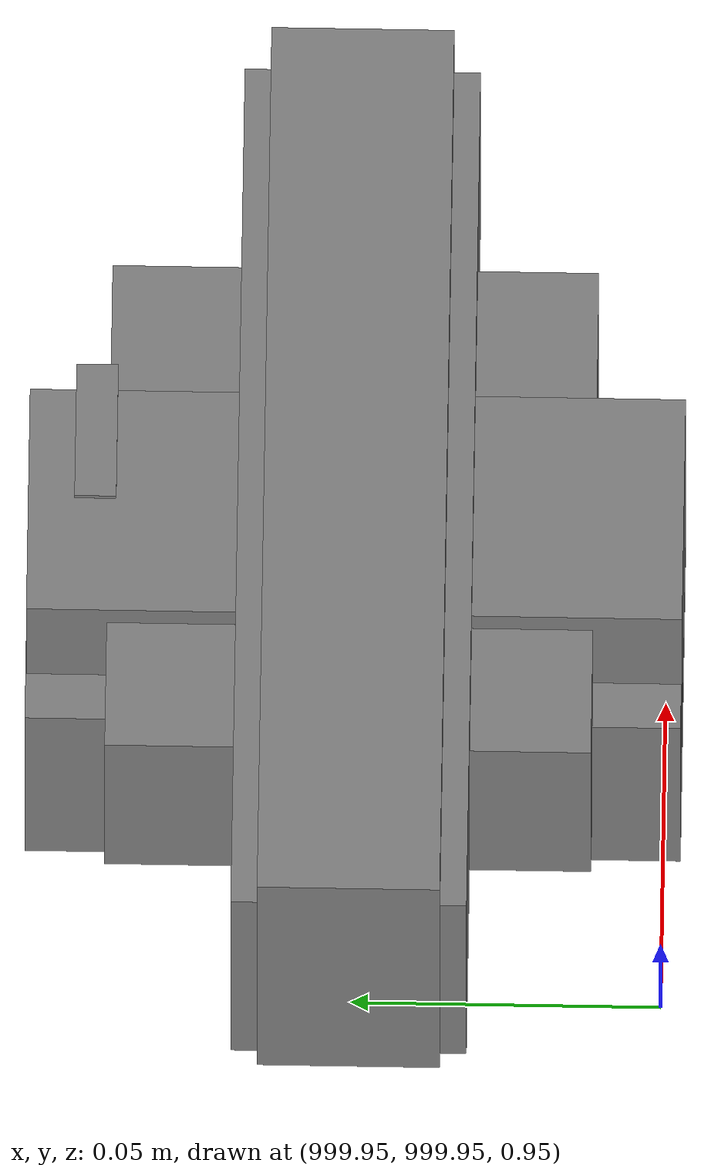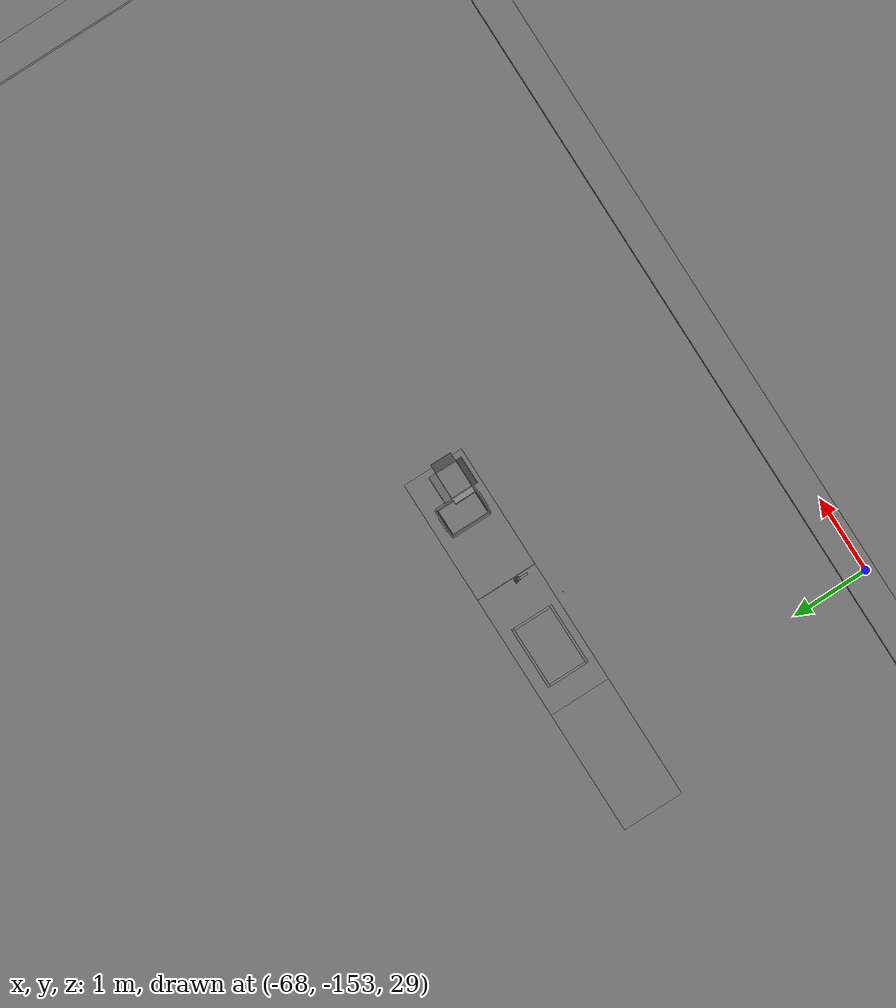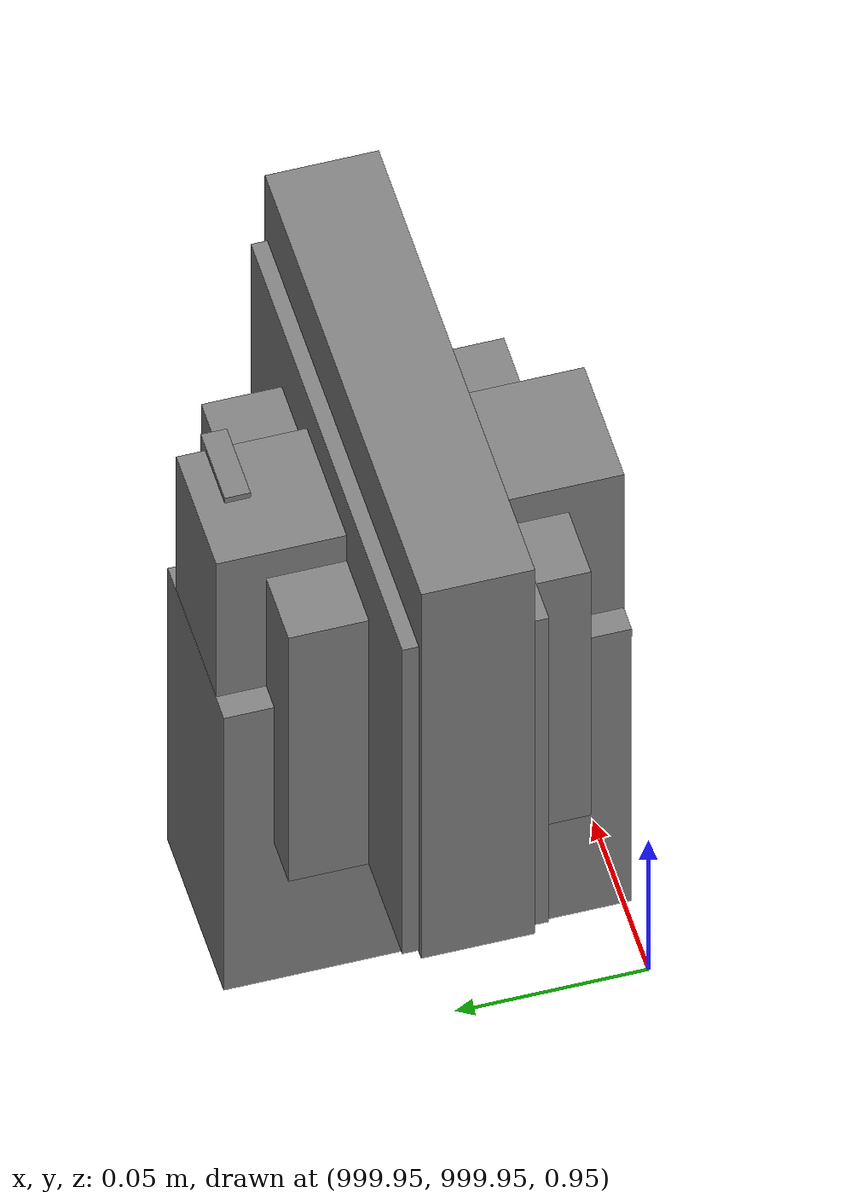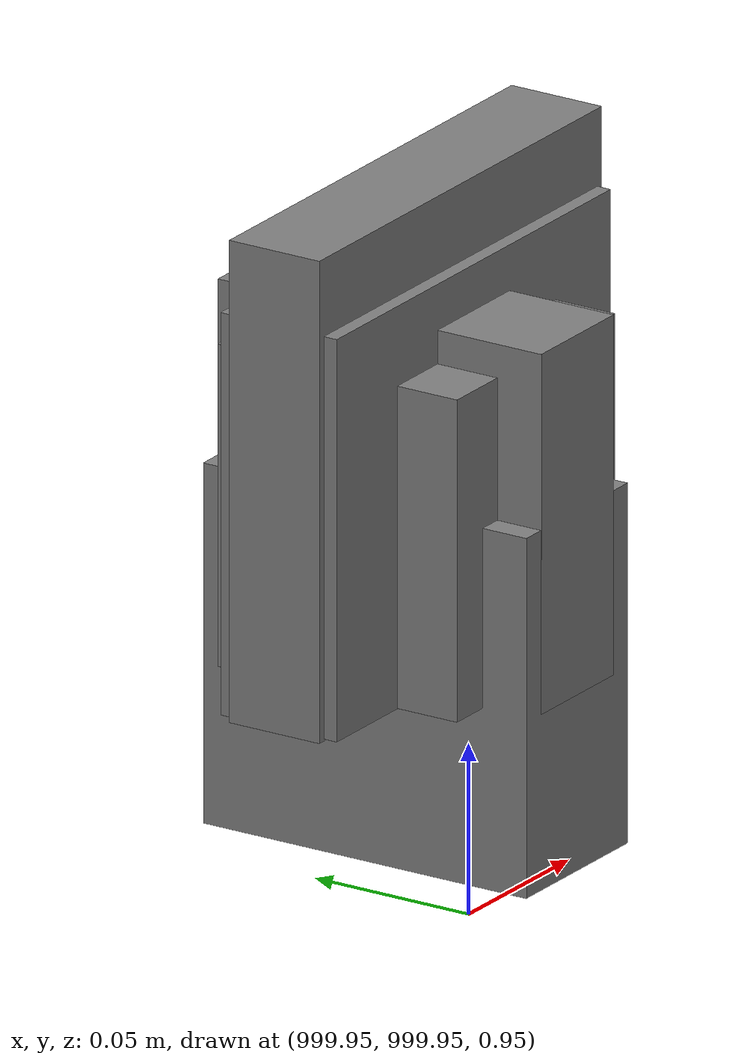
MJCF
<mujoco>
    <option gravity="0.000000000 0.000000000 -9.810000420" timestep="0.0049999999" integrator="implicitfast" density="1.225" viscosity="1.8000001e-05" noslip_iterations="10" iterations="100" sdf_iterations="50">
        <flag multiccd="disable"/>
    </option>
    <size memory="1000M"/>
    <compiler coordinate="local"/>
    <worldbody>
        <light cutoff="30" pos="0 1 1" dir="0 -1 -2"/>
        <light cutoff="30" pos="0 -1 1" dir="0 1 -2"/>
        <body pos="1000.000000000 1000.000000000 1.000000000" euler="0.000011953 0.000005123 -179.999984741" name="openloong_gripper_2f85_fix_base_usda_intel_box">
            <geom contype="1" conaffinity="1" density="1000" type="box" material="" rgba="0.500000000 0.500000000 0.500000000 1.000000000" solimp="0.899999976 0.949999988 0.001000000" friction="1.000000000 0.005000000 0.000100000" solref="0.020000000 1.000000000" margin="0" condim="3" group="0" pos="0.000000000 -0.000067139 0.000082284" quat="0.707106709 0.000000225 0.000000253 0.707106650" size="0.052800003 0.025300000 0.052800003" name="openloong_gripper_2f85_fix_base_usda_geom_D72C745E_46B9_49BE_A266_DFD248BC92D2"/>
            <freejoint name="openloong_gripper_2f85_fix_base_usda_intel_box_joint"/>
            <site size="0.005000000 0.005000000 0.005000000" rgba="0.500000000 0.500000000 0.500000000 1.000000000" pos="0.000000000 0.000000000 0.000000000" quat="0.999961913 0.008726500 0.000000000 0.000000000" group="0" type="sphere" name="openloong_gripper_2f85_fix_base_usda_intel_boxsite"/>
        </body>
        <body pos="-65.992866516 -149.472091675 31.170293808" euler="19.512886047 26.396350861 79.007591248" mocap="true" name="spotlight5_SpotLight"/>
        <body pos="1000.000000000 999.999938965 1.000000000" euler="0.000000000 0.000000000 180.000000000" name="openloong_gripper_2f85_fix_base_usda_intelcore_i5">
            <geom contype="1" conaffinity="1" density="1000" type="box" material="" rgba="0.500000000 0.500000000 0.500000000 1.000000000" solimp="0.899999976 0.949999988 0.001000000" friction="1.000000000 0.005000000 0.000100000" solref="0.020000000 1.000000000" margin="0" condim="3" group="0" pos="0.000000000 0.000000000 0.051722717" quat="0.707106709 0.000000000 0.000000000 -0.707106769" size="0.052800000 0.018080002 0.052800000" name="openloong_gripper_2f85_fix_base_usda_geom_0E985DF8_2325_46D7_AA14_A8CF4F32FA83"/>
            <freejoint name="openloong_gripper_2f85_fix_base_usda_intelcore_i5_joint"/>
            <site size="0.005000000 0.005000000 0.005000000" rgba="0.500000000 0.500000000 0.500000000 1.000000000" pos="0.000000000 0.000000000 0.000000000" quat="0.999961913 0.008726534 0.000000000 0.000000000" group="0" type="sphere" name="openloong_gripper_2f85_fix_base_usda_intelcore_i5site"/>
        </body>
        <body pos="1000.000000000 1000.000000000 1.000000000" euler="0.000000000 0.000000000 180.000000000" name="openloong_gripper_2f85_fix_base_usda_wifi_box">
            <geom contype="1" conaffinity="1" density="1000" type="box" material="" rgba="0.500000000 0.500000000 0.500000000 1.000000000" solimp="0.899999976 0.949999988 0.001000000" friction="1.000000000 0.005000000 0.000100000" solref="0.020000000 1.000000000" margin="0" condim="3" group="0" pos="0.000000000 0.000000000 0.058978677" quat="0.000000000 0.000000047 0.000000000 1.000000000" size="0.068499997 0.018999999 0.059000000" name="openloong_gripper_2f85_fix_base_usda_geom_273C9D94_081A_4D59_ACB2_A32F891CAC23"/>
            <freejoint name="openloong_gripper_2f85_fix_base_usda_wifi_box_joint"/>
            <site size="0.005000000 0.005000000 0.005000000" rgba="0.500000000 0.500000000 0.500000000 1.000000000" pos="0.000000000 0.000000000 0.000000000" quat="0.999961913 0.008726500 0.000000000 0.000000000" group="0" type="sphere" name="openloong_gripper_2f85_fix_base_usda_wifi_boxsite"/>
        </body>
        <body pos="-66.012809753 -149.501174927 31.169570923" euler="-47.015380859 64.951583862 2.314358711" mocap="true" name="spotlight1_SpotLight"/>
        <body pos="1000.000000000 1000.000000000 1.000000000" euler="0.000000000 0.000000000 180.000000000" name="openloong_gripper_2f85_fix_base_usda_cpu_fan">
            <geom contype="1" conaffinity="1" density="1000" type="box" material="" rgba="0.500000000 0.500000000 0.500000000 1.000000000" solimp="0.899999976 0.949999988 0.001000000" friction="1.000000000 0.005000000 0.000100000" solref="0.020000000 1.000000000" margin="0" condim="3" group="0" pos="0.000000000 0.000000000 0.070034981" quat="0.000000000 0.000000000 0.000000000 1.000000000" size="0.070700005 0.014699999 0.070700005" name="openloong_gripper_2f85_fix_base_usda_geom_600381B5_2E52_484C_9992_17E6A3FDA693"/>
            <freejoint name="openloong_gripper_2f85_fix_base_usda_cpu_fan_joint"/>
            <site size="0.005000000 0.005000000 0.005000000" rgba="0.500000000 0.500000000 0.500000000 1.000000000" pos="0.000000000 0.000000000 0.000000000" quat="0.999961913 0.008726535 0.000000000 0.000000000" group="0" type="sphere" name="openloong_gripper_2f85_fix_base_usda_cpu_fancsite"/>
        </body>
        <body pos="1000.000000000 1000.000000000 1.000000000" euler="0.000000000 0.000000000 180.000000000" name="openloong_gripper_2f85_fix_base_usda_battery_01">
            <geom contype="1" conaffinity="1" density="1000" type="box" material="" rgba="0.500000000 0.500000000 0.500000000 1.000000000" solimp="0.899999976 0.949999988 0.001000000" friction="1.000000000 0.005000000 0.000100000" solref="0.020000000 1.000000000" margin="0" condim="3" group="0" pos="-0.011123657 -0.041940309 0.101691343" quat="1.000000000 0.000000000 0.000000000 0.000000000" size="0.010800000 0.003375000 0.004725000" name="openloong_gripper_2f85_fix_base_usda_geom_07CFDFB5_3C2A_4BED_9F86_472E8B166012"/>
            <geom contype="1" conaffinity="1" density="1000" type="box" material="" rgba="0.500000000 0.500000000 0.500000000 1.000000000" solimp="0.899999976 0.949999988 0.001000000" friction="1.000000000 0.005000000 0.000100000" solref="0.020000000 1.000000000" margin="0" condim="3" group="0" pos="-0.010876465 -0.044247437 0.047066893" quat="0.998702705 -0.050920475 0.000000000 0.000000000" size="0.009450001 0.002700000 0.024975000" name="openloong_gripper_2f85_fix_base_usda_geom_9A56EBE9_2B5A_475B_9A77_F617188F0B6C"/>
            <geom contype="1" conaffinity="1" density="1000" type="box" material="" rgba="0.500000000 0.500000000 0.500000000 1.000000000" solimp="0.899999976 0.949999988 0.001000000" friction="1.000000000 0.005000000 0.000100000" solref="0.020000000 1.000000000" margin="0" condim="3" group="0" pos="-0.001235962 -0.000659180 0.047381196" quat="1.000000000 0.000000000 0.000000000 0.000000000" size="0.039420001 0.039150000 0.047250003" name="openloong_gripper_2f85_fix_base_usda_geom_E5A167A1_1D9B_4EAC_8211_7A913C13EE08"/>
            <geom contype="1" conaffinity="1" density="1000" type="box" material="" rgba="0.500000000 0.500000000 0.500000000 1.000000000" solimp="0.899999976 0.949999988 0.001000000" friction="1.000000000 0.005000000 0.000100000" solref="0.020000000 1.000000000" margin="0" condim="3" group="0" pos="-0.010876465 -0.039138794 0.009851727" quat="1.000000000 0.000000000 0.000000000 0.000000000" size="0.009450001 0.010800000 0.013500000" name="openloong_gripper_2f85_fix_base_usda_geom_88305F4C_AE50_4AD8_9528_CE7474162638"/>
            <geom contype="1" conaffinity="1" density="1000" type="box" material="" rgba="0.500000000 0.500000000 0.500000000 1.000000000" solimp="0.899999976 0.949999988 0.001000000" friction="1.000000000 0.005000000 0.000100000" solref="0.020000000 1.000000000" margin="0" condim="3" group="0" pos="-0.010876465 -0.041528322 0.071508206" quat="1.000000000 0.000000000 0.000000000 0.000000000" size="0.009450001 0.002700000 0.027000001" name="openloong_gripper_2f85_fix_base_usda_geom_01A35366_3212_4724_8A74_8136B1470911"/>
            <freejoint name="openloong_gripper_2f85_fix_base_usda_battery_01_joint"/>
            <site size="0.005000000 0.005000000 0.005000000" rgba="0.500000000 0.500000000 0.500000000 1.000000000" pos="0.000000000 0.000000000 0.000000000" quat="0.999961913 0.008726500 0.000000000 0.000000000" group="0" type="sphere" name="openloong_gripper_2f85_fix_base_usda_battery_01site"/>
        </body>
        <body pos="-66.035972595 -148.887435913 31.162538528" euler="118.030471802 83.849594116 70.685844421" mocap="true" name="spotlight4_SpotLight"/>
        <body pos="-64.866622925 -149.383972168 30.183746338" euler="89.999984741 89.999946594 0.000000000" name="openloong_gripper_2f85_fix_base_usda_bluebox_01">
            <geom contype="1" conaffinity="1" density="1000" type="box" material="" rgba="0.500000000 0.500000000 0.500000000 1.000000000" solimp="0.899999976 0.949999988 0.001000000" friction="1.000000000 0.005000000 0.000100000" solref="0.020000000 1.000000000" margin="0" condim="3" group="0" pos="0.276580811 0.187225342 0.000068665" quat="0.707106948 0.000077471 0.707106352 0.000077486" size="0.100000001 0.057999998 0.010000000" name="openloong_gripper_2f85_fix_base_usda_geom_E8330F4D_9BC4_4C77_B2A0_BDA9BD1E24A1"/>
            <geom contype="1" conaffinity="1" density="1000" type="box" material="" rgba="0.500000000 0.500000000 0.500000000 1.000000000" solimp="0.899999976 0.949999988 0.001000000" friction="1.000000000 0.005000000 0.000100000" solref="0.020000000 1.000000000" margin="0" condim="3" group="0" pos="0.000000000 0.002883911 0.000000000" quat="0.999999881 0.000000000 0.000000000 0.000000000" size="0.254000008 0.003000000 0.172000006" name="openloong_gripper_2f85_fix_base_usda_geom_A9B6AAFB_A7F6_4604_91F0_4EB1AA7C4EC3"/>
            <geom contype="1" conaffinity="1" density="1000" type="box" material="" rgba="0.500000000 0.500000000 0.500000000 1.000000000" solimp="0.899999976 0.949999988 0.001000000" friction="1.000000000 0.005000000 0.000100000" solref="0.020000000 1.000000000" margin="0" condim="3" group="0" pos="0.000000000 0.124874115 0.173484802" quat="0.999796331 0.020176515 -0.000000015 0.000000030" size="0.259999990 0.119999997 0.007000000" name="openloong_gripper_2f85_fix_base_usda_geom_861E5975_7204_47A5_BFD7_7F81DF08C3D4"/>
            <geom contype="1" conaffinity="1" density="1000" type="box" material="" rgba="0.500000000 0.500000000 0.500000000 1.000000000" solimp="0.899999976 0.949999988 0.001000000" friction="1.000000000 0.005000000 0.000100000" solref="0.020000000 1.000000000" margin="0" condim="3" group="0" pos="0.000000000 0.124874115 -0.173469543" quat="0.999796331 -0.020176545 -0.000000015 0.000000000" size="0.259999990 0.119999997 0.007000000" name="openloong_gripper_2f85_fix_base_usda_geom_07868033_2031_47CF_A4C7_CE1F3FA726DE"/>
            <geom contype="1" conaffinity="1" density="1000" type="box" material="" rgba="0.500000000 0.500000000 0.500000000 1.000000000" solimp="0.899999976 0.949999988 0.001000000" friction="1.000000000 0.005000000 0.000100000" solref="0.020000000 1.000000000" margin="0" condim="3" group="0" pos="0.000000000 0.214008331 0.188980103" quat="0.999912977 0.013176724 0.000000015 0.000000000" size="0.259999990 0.029999999 0.012500000" name="openloong_gripper_2f85_fix_base_usda_geom_F7E4B504_3F91_493D_AB08_EF6B14228B03"/>
            <geom contype="1" conaffinity="1" density="1000" type="box" material="" rgba="0.500000000 0.500000000 0.500000000 1.000000000" solimp="0.899999976 0.949999988 0.001000000" friction="1.000000000 0.005000000 0.000100000" solref="0.020000000 1.000000000" margin="0" condim="3" group="0" pos="-0.258361816 0.125289917 0.001876831" quat="0.702796936 -0.020792112 0.710783124 0.020769298" size="0.189999998 0.119999997 0.009000000" name="openloong_gripper_2f85_fix_base_usda_geom_54F50770_DF80_472F_8BB4_6B2C45CEEFAB"/>
            <geom contype="1" conaffinity="1" density="1000" type="box" material="" rgba="0.500000000 0.500000000 0.500000000 1.000000000" solimp="0.899999976 0.949999988 0.001000000" friction="1.000000000 0.005000000 0.000100000" solref="0.020000000 1.000000000" margin="0" condim="3" group="0" pos="0.000000000 0.214008331 -0.188980103" quat="0.999912977 -0.013176769 0.000000030 0.000000015" size="0.259999990 0.029999999 0.012500000" name="openloong_gripper_2f85_fix_base_usda_geom_C44C952B_07C5_4946_87B5_0537BA307F6E"/>
            <geom contype="1" conaffinity="1" density="1000" type="box" material="" rgba="0.500000000 0.500000000 0.500000000 1.000000000" solimp="0.899999976 0.949999988 0.001000000" friction="1.000000000 0.005000000 0.000100000" solref="0.020000000 1.000000000" margin="0" condim="3" group="0" pos="-0.276611328 0.187225342 0.000068665" quat="0.707106650 0.000077441 0.707106709 0.000077456" size="0.100000001 0.057999998 0.010000000" name="openloong_gripper_2f85_fix_base_usda_geom_49A29754_70D2_49D8_A245_0A51A7D826B1"/>
            <geom contype="1" conaffinity="1" density="1000" type="box" material="" rgba="0.500000000 0.500000000 0.500000000 1.000000000" solimp="0.899999976 0.949999988 0.001000000" friction="1.000000000 0.005000000 0.000100000" solref="0.020000000 1.000000000" margin="0" condim="3" group="0" pos="0.258331299 0.125289917 0.001876831" quat="0.702851415 0.018856421 0.710823774 -0.019329369" size="0.189999998 0.119999997 0.009000000" name="openloong_gripper_2f85_fix_base_usda_geom_AD19EAA6_12F3_48D7_B8DA_7A8936B6A0FB"/>
            <freejoint name="openloong_gripper_2f85_fix_base_usda_bluebox_01_joint"/>
            <site size="0.005000000 0.005000000 0.005000000" rgba="0.500000000 0.500000000 0.500000000 1.000000000" pos="0.000000000 0.000000000 0.000000000" quat="0.999961913 0.008726534 0.000000000 0.000000000" group="0" type="sphere" name="openloong_gripper_2f85_fix_base_usda_bluebox_01site"/>
        </body>
        <body pos="-64.496299744 -149.491867065 30.235729218" euler="0.000000000 0.000000000 89.999946594" name="openloong_gripper_2f85_fix_base_usda_cardboardbox_01">
            <geom contype="1" conaffinity="1" density="1000" type="box" material="" rgba="0.500000000 0.500000000 0.500000000 1.000000000" solimp="0.899999976 0.949999988 0.001000000" friction="1.000000000 0.005000000 0.000100000" solref="0.020000000 1.000000000" margin="0" condim="3" group="0" pos="-0.003166199 -0.004086494 0.005052090" quat="1.000000000 0.000000000 0.000000000 0.000000000" size="0.142499998 0.177500010 0.005000000" name="openloong_gripper_2f85_fix_base_usda_geom_DA667EB8_9D70_43E9_9D57_B340F00BD7CE"/>
            <geom contype="1" conaffinity="1" density="1000" type="box" material="" rgba="0.500000000 0.500000000 0.500000000 1.000000000" solimp="0.899999976 0.949999988 0.001000000" friction="1.000000000 0.005000000 0.000100000" solref="0.020000000 1.000000000" margin="0" condim="3" group="0" pos="-0.003166199 0.170316696 0.150570869" quat="1.000000000 0.000000000 0.000000000 0.000000000" size="0.142499998 0.005000000 0.149999991" name="openloong_gripper_2f85_fix_base_usda_geom_62EEAFD8_6E7B_49E9_BE24_680B0A7414B2"/>
            <geom contype="1" conaffinity="1" density="1000" type="box" material="" rgba="0.500000000 0.500000000 0.500000000 1.000000000" solimp="0.899999976 0.949999988 0.001000000" friction="1.000000000 0.005000000 0.000100000" solref="0.020000000 1.000000000" margin="0" condim="3" group="0" pos="-0.147399902 -0.005307198 0.150570869" quat="1.000000000 0.000000000 0.000000000 0.000000000" size="0.005000000 0.177500010 0.149999991" name="openloong_gripper_2f85_fix_base_usda_geom_28B8CE89_BE9F_4087_B3C8_4D80EB2F0394"/>
            <geom contype="1" conaffinity="1" density="1000" type="box" material="" rgba="0.500000000 0.500000000 0.500000000 1.000000000" solimp="0.899999976 0.949999988 0.001000000" friction="1.000000000 0.005000000 0.000100000" solref="0.020000000 1.000000000" margin="0" condim="3" group="0" pos="0.140275955 -0.005307198 0.150570869" quat="1.000000000 0.000000000 0.000000000 0.000000000" size="0.005000000 0.177500010 0.149999991" name="openloong_gripper_2f85_fix_base_usda_geom_13F105E6_F06B_4E9D_8E94_6D6506B3D050"/>
            <geom contype="1" conaffinity="1" density="1000" type="box" material="" rgba="0.500000000 0.500000000 0.500000000 1.000000000" solimp="0.899999976 0.949999988 0.001000000" friction="1.000000000 0.005000000 0.000100000" solref="0.020000000 1.000000000" margin="0" condim="3" group="0" pos="-0.003166199 -0.181550980 0.150570869" quat="1.000000000 0.000000000 0.000000000 0.000000000" size="0.142499998 0.005000000 0.149999991" name="openloong_gripper_2f85_fix_base_usda_geom_17C5DA93_CE1A_4959_93F3_644624330DBE"/>
            <freejoint name="openloong_gripper_2f85_fix_base_usda_cardboardbox_01_joint"/>
            <site size="0.005000000 0.005000000 0.005000000" rgba="0.500000000 0.500000000 0.500000000 1.000000000" pos="0.000000000 0.000000000 0.000000000" quat="0.999961913 0.008726535 0.000000000 0.000000000" group="0" type="sphere" name="openloong_gripper_2f85_fix_base_usda_site_1256456D_48AF_4A86_871F_7899D3B525D5"/>
            <body pos="0.139160156 -0.004048347 0.301930904" euler="-179.999954224 49.383502960 179.999954224" name="openloong_gripper_2f85_fix_base_usda_A1_006">
                <geom contype="1" conaffinity="1" density="1000" type="box" material="" rgba="0.500000000 0.500000000 0.500000000 1.000000000" solimp="0.899999976 0.949999988 0.001000000" friction="1.000000000 0.005000000 0.000100000" solref="0.020000000 1.000000000" margin="0" condim="3" group="0" pos="-0.071587563 0.000009537 0.001745224" quat="0.999999881 0.000000000 0.000000000 0.000000000" size="0.071249999 0.179999992 0.002500000" name="openloong_gripper_2f85_fix_base_usda_geom_95799DE8_5121_4C62_8364_C923CBA13369"/>
                <joint armature="0" stiffness="0.07" damping="0.0099999998" axis="0.000000 1.000000 0.000000" type="hinge" name="openloong_gripper_2f85_fix_base_usda_A1_006"/>
            </body>
            <body pos="-0.145902634 -0.004086494 0.301938057" euler="-180.000000000 -60.000011444 -180.000000000" name="openloong_gripper_2f85_fix_base_usda_A2_006">
                <geom contype="1" conaffinity="1" density="1000" type="box" material="" rgba="0.500000000 0.500000000 0.500000000 1.000000000" solimp="0.899999976 0.949999988 0.001000000" friction="1.000000000 0.005000000 0.000100000" solref="0.020000000 1.000000000" margin="0" condim="3" group="0" pos="0.071268082 0.000009537 0.002717972" quat="0.000002921 0.000000000 -0.000000030 0.999999881" size="0.071249999 0.179999992 0.002500000" name="openloong_gripper_2f85_fix_base_usda_geom_62EAC65A_9977_4D45_9BD3_D2467175EEDB"/>
                <joint armature="0" stiffness="0.07" damping="0.0099999998" axis="0.000000 1.000000 0.000000" type="hinge" name="openloong_gripper_2f85_fix_base_usda_A2_006"/>
            </body>
            <body pos="-0.003385544 0.175991058 0.301930904" euler="-125.858116150 -0.000004561 0.000002331" name="openloong_gripper_2f85_fix_base_usda_B2_006">
                <geom contype="1" conaffinity="1" density="1000" type="box" material="" rgba="0.500000000 0.500000000 0.500000000 1.000000000" solimp="0.899999976 0.949999988 0.001000000" friction="1.000000000 0.005000000 0.000100000" solref="0.020000000 1.000000000" margin="0" condim="3" group="0" pos="0.000009537 -0.070939064 -0.002470016" quat="0.999614120 0.027776197 -0.000000015 0.000000030" size="0.137500003 0.064999998 0.005000000" name="openloong_gripper_2f85_fix_base_usda_geom_91615DBE_0F72_4D18_9B10_8703E7F338E7"/>
                <joint armature="0" stiffness="0.07" damping="0.0099999998" axis="1.000000 0.000000 0.000000" type="hinge" name="openloong_gripper_2f85_fix_base_usda_B2_006"/>
            </body>
            <body pos="-0.003385544 -0.184140205 0.301938057" euler="147.805557251 0.000000000 0.000000000" name="openloong_gripper_2f85_fix_base_usda_B1_006">
                <geom contype="1" conaffinity="1" density="1000" type="box" material="" rgba="0.500000000 0.500000000 0.500000000 1.000000000" solimp="0.899999976 0.949999988 0.001000000" friction="1.000000000 0.005000000 0.000100000" solref="0.020000000 1.000000000" margin="0" condim="3" group="0" pos="-0.000028610 0.070202351 -0.002703667" quat="0.999614179 -0.027776167 0.000000000 0.000000000" size="0.137500003 0.064999998 0.005000000" name="openloong_gripper_2f85_fix_base_usda_geom_D7D70BFF_D02B_4788_B496_B7B47B4F357E"/>
                <joint armature="0" stiffness="0.07" damping="0.0099999998" axis="1.000000 0.000000 0.000000" type="hinge" name="openloong_gripper_2f85_fix_base_usda_B1_006"/>
            </body>
        </body>
        <body pos="-65.882858276 -149.481979370 30.229999542" euler="-64.487716675 0.000000000 0.000000000" name="openloong_gripper_2f85_fix_base_usda_Barcode">
            <geom contype="1" conaffinity="1" density="1000" type="box" material="" rgba="0.500000000 0.500000000 0.500000000 1.000000000" solimp="0.899999976 0.949999988 0.001000000" friction="1.000000000 0.005000000 0.000100000" solref="0.020000000 1.000000000" margin="0" condim="3" group="0" pos="0.000000000 0.013038635 0.001419067" quat="0.000000000 0.000000000 0.000000000 1.000000119" size="0.034000002 0.010000000 0.017999999" name="openloong_gripper_2f85_fix_base_usda_geom_A74AE6F9_C5C6_47A1_8BED_888E377ACD42"/>
            <geom contype="1" conaffinity="1" density="1000" type="box" material="" rgba="0.500000000 0.500000000 0.500000000 1.000000000" solimp="0.899999976 0.949999988 0.001000000" friction="1.000000000 0.005000000 0.000100000" solref="0.020000000 1.000000000" margin="0" condim="3" group="0" pos="0.000000000 -0.035301208 -0.007095337" quat="0.000000000 0.000000000 -0.043619365 0.999048233" size="0.028999999 0.010000000 0.020000000" name="openloong_gripper_2f85_fix_base_usda_geom_E4B29FD9_766C_4A95_BFE4_DF0D79A4C010"/>
            <geom contype="1" conaffinity="1" density="1000" type="box" material="" rgba="0.500000000 0.500000000 0.500000000 1.000000000" solimp="0.899999976 0.949999988 0.001000000" friction="1.000000000 0.005000000 0.000100000" solref="0.020000000 1.000000000" margin="0" condim="3" group="0" pos="0.000000000 -0.043411255 -0.011749268" quat="0.922262907 0.386563420 0.000000000 0.000000000" size="0.026000001 0.010000000 0.020000000" name="openloong_gripper_2f85_fix_base_usda_geom_D2271783_195E_469F_87E9_2BBAA0897544"/>
            <geom contype="1" conaffinity="1" density="1000" type="box" material="" rgba="0.500000000 0.500000000 0.500000000 1.000000000" solimp="0.899999976 0.949999988 0.001000000" friction="1.000000000 0.005000000 0.000100000" solref="0.020000000 1.000000000" margin="0" condim="3" group="0" pos="0.000000000 -0.016967773 -0.031860352" quat="0.000000000 0.000000000 0.000000000 1.000000119" size="0.008000000 0.010000000 0.013000000" name="openloong_gripper_2f85_fix_base_usda_geom_9DEB2748_2B6F_44CF_A194_A8E86F6F82C9"/>
            <geom contype="1" conaffinity="1" density="1000" type="box" material="" rgba="0.500000000 0.500000000 0.500000000 1.000000000" solimp="0.899999976 0.949999988 0.001000000" friction="1.000000000 0.005000000 0.000100000" solref="0.020000000 1.000000000" margin="0" condim="3" group="0" pos="0.000000000 -0.001869202 0.000312805" quat="0.953716993 0.300705761 0.000000000 0.000000000" size="0.032000002 0.010000000 0.018999999" name="openloong_gripper_2f85_fix_base_usda_geom_56E9A72D_0940_46FB_BEE5_D63948996D09"/>
            <geom contype="1" conaffinity="1" density="1000" type="box" material="" rgba="0.500000000 0.500000000 0.500000000 1.000000000" solimp="0.899999976 0.949999988 0.001000000" friction="1.000000000 0.005000000 0.000100000" solref="0.020000000 1.000000000" margin="0" condim="3" group="0" pos="0.000000000 -0.019531250 -0.003173828" quat="0.953716993 0.300705761 0.000000000 0.000000000" size="0.030999999 0.010000000 0.020000000" name="openloong_gripper_2f85_fix_base_usda_geom_C74BBF93_80F8_482F_ACFB_A1D5783BC8F1"/>
            <geom contype="1" conaffinity="1" density="1000" type="box" material="" rgba="0.500000000 0.500000000 0.500000000 1.000000000" solimp="0.899999976 0.949999988 0.001000000" friction="1.000000000 0.005000000 0.000100000" solref="0.020000000 1.000000000" margin="0" condim="3" group="0" pos="0.000000000 -0.035301208 -0.007095337" quat="0.953716993 0.300705761 0.000000000 0.000000000" size="0.028999999 0.010000000 0.020000000" name="openloong_gripper_2f85_fix_base_usda_geom_978A0546_1F78_47DD_80B3_E249333F9CBD"/>
            <geom contype="1" conaffinity="1" density="1000" type="box" material="" rgba="0.500000000 0.500000000 0.500000000 1.000000000" solimp="0.899999976 0.949999988 0.001000000" friction="1.000000000 0.005000000 0.000100000" solref="0.020000000 1.000000000" margin="0" condim="3" group="0" pos="0.000000000 -0.042617798 -0.071121216" quat="0.000000000 0.000000000 0.000000000 1.000000119" size="0.013000000 0.021000000 0.059999999" name="openloong_gripper_2f85_fix_base_usda_geom_F82A05A0_48B3_4B1E_B7AA_B2804F6FC241"/>
            <freejoint name="openloong_gripper_2f85_fix_base_usda_Barcode_joint"/>
            <site size="0.005000000 0.005000000 0.005000000" rgba="0.500000000 0.500000000 0.500000000 1.000000000" pos="0.000000000 0.000000000 0.000000000" quat="1.000000000 0.000000000 0.000000000 0.000000000" group="0" type="sphere" name="openloong_gripper_2f85_fix_base_usda_Barcode_site"/>
        </body>
        <body pos="-66.745018005 -149.392349243 30.184000015" euler="0.000000000 0.000000000 89.999946594" name="[22333665667600]_Basket_01">
            <geom contype="1" conaffinity="1" density="1000" type="box" material="" rgba="0.500000000 0.500000000 0.500000000 1.000000000" solimp="0.899999976 0.949999988 0.001000000" friction="1.000000000 0.005000000 0.000100000" solref="0.020000000 1.000000000" margin="0" condim="3" group="0" pos="-0.052425385 0.389207840 0.089787483" quat="0.707107008 0.000000000 0.000000000 0.707106411" size="0.014249999 0.014249999 0.059999999" name="[22333665667600]_geom_5D209A29_B04F_4224_8028_445BE66BED3A"/>
            <geom contype="1" conaffinity="1" density="1000" type="box" material="" rgba="0.500000000 0.500000000 0.500000000 1.000000000" solimp="0.899999976 0.949999988 0.001000000" friction="1.000000000 0.005000000 0.000100000" solref="0.020000000 1.000000000" margin="0" condim="3" group="0" pos="0.264015198 -0.133043289 0.089787483" quat="0.707107008 0.000000000 0.000000000 0.707106411" size="0.014249999 0.014249999 0.059999999" name="[22333665667600]_geom_25D2F0CF_0518_4974_B1CF_A7C7BCE2C26E"/>
            <geom contype="1" conaffinity="1" density="1000" type="box" material="" rgba="0.500000000 0.500000000 0.500000000 1.000000000" solimp="0.899999976 0.949999988 0.001000000" friction="1.000000000 0.005000000 0.000100000" solref="0.020000000 1.000000000" margin="0" condim="3" group="0" pos="-0.264015198 -0.265548706 0.089793205" quat="0.707107008 0.000000000 0.000000000 0.707106411" size="0.014249999 0.014249999 0.059999999" name="[22333665667600]_geom_A6A3B124_45A3_4F48_9EEE_83C16CB514DB"/>
            <geom contype="1" conaffinity="1" density="1000" type="box" material="" rgba="0.500000000 0.500000000 0.500000000 1.000000000" solimp="0.899999976 0.949999988 0.001000000" friction="1.000000000 0.005000000 0.000100000" solref="0.020000000 1.000000000" margin="0" condim="3" group="0" pos="-0.160263062 -0.389322281 0.089793205" quat="0.707107008 0.000000000 0.000000000 0.707106411" size="0.014249999 0.014249999 0.059999999" name="[22333665667600]_geom_FF4B4E85_F922_4AD0_868B_2B6FB4F07DE9"/>
            <geom contype="1" conaffinity="1" density="1000" type="box" material="" rgba="0.500000000 0.500000000 0.500000000 1.000000000" solimp="0.899999976 0.949999988 0.001000000" friction="1.000000000 0.005000000 0.000100000" solref="0.020000000 1.000000000" margin="0" condim="3" group="0" pos="0.162265778 -0.389322281 0.089787483" quat="0.707107008 0.000000000 0.000000000 0.707106411" size="0.014249999 0.014249999 0.059999999" name="[22333665667600]_geom_110A59CF_EE52_45B3_A5E1_68A880FB2E8B"/>
            <geom contype="1" conaffinity="1" density="1000" type="box" material="" rgba="0.500000000 0.500000000 0.500000000 1.000000000" solimp="0.899999976 0.949999988 0.001000000" friction="1.000000000 0.005000000 0.000100000" solref="0.020000000 1.000000000" margin="0" condim="3" group="0" pos="0.264015198 0.389207840 0.089787483" quat="0.707107008 0.000000000 0.000000000 0.707106411" size="0.014249999 0.014249999 0.059999999" name="[22333665667600]_geom_A72C5203_71F3_40F7_B2B5_AD8A79DC9723"/>
            <geom contype="1" conaffinity="1" density="1000" type="box" material="" rgba="0.500000000 0.500000000 0.500000000 1.000000000" solimp="0.899999976 0.949999988 0.001000000" friction="1.000000000 0.005000000 0.000100000" solref="0.020000000 1.000000000" margin="0" condim="3" group="0" pos="-0.264015198 -0.133043289 0.089793205" quat="0.707107008 0.000000000 0.000000000 0.707106411" size="0.014249999 0.014249999 0.059999999" name="[22333665667600]_geom_8C73815D_15CA_48EF_8AD0_7C15DB789EAC"/>
            <geom contype="1" conaffinity="1" density="1000" type="box" material="" rgba="0.500000000 0.500000000 0.500000000 1.000000000" solimp="0.899999976 0.949999988 0.001000000" friction="1.000000000 0.005000000 0.000100000" solref="0.020000000 1.000000000" margin="0" condim="3" group="0" pos="-0.264026642 0.269256592 0.089793205" quat="0.707107008 0.000000000 0.000000000 0.707106411" size="0.014249999 0.014249999 0.059999999" name="[22333665667600]_geom_0150FC3F_1E39_4AB5_92D1_E638D31A0066"/>
            <geom contype="1" conaffinity="1" density="1000" type="box" material="" rgba="0.500000000 0.500000000 0.500000000 1.000000000" solimp="0.899999976 0.949999988 0.001000000" friction="1.000000000 0.005000000 0.000100000" solref="0.020000000 1.000000000" margin="0" condim="3" group="0" pos="0.054462433 0.389207840 0.089787483" quat="0.707107008 0.000000000 0.000000000 0.707106411" size="0.014249999 0.014249999 0.059999999" name="[22333665667600]_geom_40F9610E_7785_43A3_A780_0098893E9200"/>
            <geom contype="1" conaffinity="1" density="1000" type="box" material="" rgba="0.500000000 0.500000000 0.500000000 1.000000000" solimp="0.899999976 0.949999988 0.001000000" friction="1.000000000 0.005000000 0.000100000" solref="0.020000000 1.000000000" margin="0" condim="3" group="0" pos="0.054462433 -0.389322281 0.089787483" quat="0.707107008 0.000000000 0.000000000 0.707106411" size="0.014249999 0.014249999 0.059999999" name="[22333665667600]_geom_C61C2111_B9E9_4D4A_A063_461778B72873"/>
            <geom contype="1" conaffinity="1" density="1000" type="box" material="" rgba="0.500000000 0.500000000 0.500000000 1.000000000" solimp="0.899999976 0.949999988 0.001000000" friction="1.000000000 0.005000000 0.000100000" solref="0.020000000 1.000000000" margin="0" condim="3" group="0" pos="0.264015198 0.269256592 0.089793205" quat="0.707107008 0.000000000 0.000000000 0.707106411" size="0.014249999 0.014249999 0.059999999" name="[22333665667600]_geom_1B5567ED_1D85_4FDE_9883_CF4EE7BA3B1B"/>
            <geom contype="1" conaffinity="1" density="1000" type="box" material="" rgba="0.500000000 0.500000000 0.500000000 1.000000000" solimp="0.899999976 0.949999988 0.001000000" friction="1.000000000 0.005000000 0.000100000" solref="0.020000000 1.000000000" margin="0" condim="3" group="0" pos="0.264015198 -0.389322281 0.089787483" quat="0.707107008 0.000000000 0.000000000 0.707106411" size="0.014249999 0.014249999 0.059999999" name="[22333665667600]_geom_DBB97D0C_2C00_4DFC_B0BC_BB6F05E05CCC"/>
            <geom contype="1" conaffinity="1" density="1000" type="box" material="" rgba="0.500000000 0.500000000 0.500000000 1.000000000" solimp="0.899999976 0.949999988 0.001000000" friction="1.000000000 0.005000000 0.000100000" solref="0.020000000 1.000000000" margin="0" condim="3" group="0" pos="0.000000000 0.000000000 0.015998840" quat="0.707107008 0.000000000 0.000000000 0.707106411" size="0.403499991 0.279000014 0.015750000" name="[22333665667600]_geom_0B25B7EF_BC32_4CC4_8BF5_7EFA0DF13EB0"/>
            <geom contype="1" conaffinity="1" density="1000" type="box" material="" rgba="0.500000000 0.500000000 0.500000000 1.000000000" solimp="0.899999976 0.949999988 0.001000000" friction="1.000000000 0.005000000 0.000100000" solref="0.020000000 1.000000000" margin="0" condim="3" group="0" pos="0.000000000 -0.389476776 0.163619041" quat="0.707107008 0.000000000 0.000000000 0.707106411" size="0.015000000 0.277500004 0.015750000" name="[22333665667600]_geom_D7888652_E3EF_4235_AD40_D1162C047A6E"/>
            <geom contype="1" conaffinity="1" density="1000" type="box" material="" rgba="0.500000000 0.500000000 0.500000000 1.000000000" solimp="0.899999976 0.949999988 0.001000000" friction="1.000000000 0.005000000 0.000100000" solref="0.020000000 1.000000000" margin="0" condim="3" group="0" pos="0.162265778 0.389207840 0.089787483" quat="0.707107008 0.000000000 0.000000000 0.707106411" size="0.014249999 0.014249999 0.059999999" name="[22333665667600]_geom_D6B265F8_38F5_48EC_83E5_180D5596A0E2"/>
            <geom contype="1" conaffinity="1" density="1000" type="box" material="" rgba="0.500000000 0.500000000 0.500000000 1.000000000" solimp="0.899999976 0.949999988 0.001000000" friction="1.000000000 0.005000000 0.000100000" solref="0.020000000 1.000000000" margin="0" condim="3" group="0" pos="0.000000000 0.389471054 0.163619041" quat="0.707107008 0.000000000 0.000000000 0.707106411" size="0.015000000 0.277500004 0.015750000" name="[22333665667600]_geom_D2C61C0A_1274_4E9E_A054_08419F1FFE42"/>
            <geom contype="1" conaffinity="1" density="1000" type="box" material="" rgba="0.500000000 0.500000000 0.500000000 1.000000000" solimp="0.899999976 0.949999988 0.001000000" friction="1.000000000 0.005000000 0.000100000" solref="0.020000000 1.000000000" margin="0" condim="3" group="0" pos="-0.263511658 0.000000000 0.163619041" quat="0.707107008 0.000000000 0.000000000 0.707106411" size="0.403499991 0.015000000 0.015750000" name="[22333665667600]_geom_2E917158_CABF_4CE2_A33B_39863695B606"/>
            <geom contype="1" conaffinity="1" density="1000" type="box" material="" rgba="0.500000000 0.500000000 0.500000000 1.000000000" solimp="0.899999976 0.949999988 0.001000000" friction="1.000000000 0.005000000 0.000100000" solref="0.020000000 1.000000000" margin="0" condim="3" group="0" pos="-0.264015198 0.141334534 0.089793205" quat="0.707107008 0.000000000 0.000000000 0.707106411" size="0.014249999 0.014249999 0.059999999" name="[22333665667600]_geom_651DDE67_E5AD_46B3_AC43_A93B306EBE4A"/>
            <geom contype="1" conaffinity="1" density="1000" type="box" material="" rgba="0.500000000 0.500000000 0.500000000 1.000000000" solimp="0.899999976 0.949999988 0.001000000" friction="1.000000000 0.005000000 0.000100000" solref="0.020000000 1.000000000" margin="0" condim="3" group="0" pos="0.264015198 -0.265548706 0.089787483" quat="0.707107008 0.000000000 0.000000000 0.707106411" size="0.014249999 0.014249999 0.059999999" name="[22333665667600]_geom_6EF9DC85_2C3B_4D82_923A_1187B529CE12"/>
            <geom contype="1" conaffinity="1" density="1000" type="box" material="" rgba="0.500000000 0.500000000 0.500000000 1.000000000" solimp="0.899999976 0.949999988 0.001000000" friction="1.000000000 0.005000000 0.000100000" solref="0.020000000 1.000000000" margin="0" condim="3" group="0" pos="-0.160263062 0.389207840 0.089787483" quat="0.707107008 0.000000000 0.000000000 0.707106411" size="0.014249999 0.014249999 0.059999999" name="[22333665667600]_geom_2AD16BA3_DB91_463E_888D_FD631CAF9B22"/>
            <geom contype="1" conaffinity="1" density="1000" type="box" material="" rgba="0.500000000 0.500000000 0.500000000 1.000000000" solimp="0.899999976 0.949999988 0.001000000" friction="1.000000000 0.005000000 0.000100000" solref="0.020000000 1.000000000" margin="0" condim="3" group="0" pos="-0.052425385 -0.389322281 0.089787483" quat="0.707107008 0.000000000 0.000000000 0.707106411" size="0.014249999 0.014249999 0.059999999" name="[22333665667600]_geom_C6596534_141A_43C5_A34D_60F93D461292"/>
            <geom contype="1" conaffinity="1" density="1000" type="box" material="" rgba="0.500000000 0.500000000 0.500000000 1.000000000" solimp="0.899999976 0.949999988 0.001000000" friction="1.000000000 0.005000000 0.000100000" solref="0.020000000 1.000000000" margin="0" condim="3" group="0" pos="-0.264026642 -0.389322281 0.089793205" quat="0.707107008 0.000000000 0.000000000 0.707106411" size="0.014249999 0.014249999 0.059999999" name="[22333665667600]_geom_89370650_82B6_4FB0_8A15_75659C55BA3C"/>
            <geom contype="1" conaffinity="1" density="1000" type="box" material="" rgba="0.500000000 0.500000000 0.500000000 1.000000000" solimp="0.899999976 0.949999988 0.001000000" friction="1.000000000 0.005000000 0.000100000" solref="0.020000000 1.000000000" margin="0" condim="3" group="0" pos="0.264015198 0.141334534 0.089787483" quat="0.707107008 0.000000000 0.000000000 0.707106411" size="0.014249999 0.014249999 0.059999999" name="[22333665667600]_geom_BB8A83C3_D6AF_485C_B968_637133CF51E1"/>
            <geom contype="1" conaffinity="1" density="1000" type="box" material="" rgba="0.500000000 0.500000000 0.500000000 1.000000000" solimp="0.899999976 0.949999988 0.001000000" friction="1.000000000 0.005000000 0.000100000" solref="0.020000000 1.000000000" margin="0" condim="3" group="0" pos="-0.264015198 0.389207840 0.089793205" quat="0.707107008 0.000000000 0.000000000 0.707106411" size="0.014249999 0.014249999 0.059999999" name="[22333665667600]_geom_A21833F9_2E45_4E3A_BBFE_0FAB5AE45DCB"/>
            <geom contype="1" conaffinity="1" density="1000" type="box" material="" rgba="0.500000000 0.500000000 0.500000000 1.000000000" solimp="0.899999976 0.949999988 0.001000000" friction="1.000000000 0.005000000 0.000100000" solref="0.020000000 1.000000000" margin="0" condim="3" group="0" pos="0.264015198 0.004480362 0.089787483" quat="0.707107008 0.000000000 0.000000000 0.707106411" size="0.014249999 0.014249999 0.059999999" name="[22333665667600]_geom_14785ACA_E48F_4399_BB27_7111BF698CA7"/>
            <geom contype="1" conaffinity="1" density="1000" type="box" material="" rgba="0.500000000 0.500000000 0.500000000 1.000000000" solimp="0.899999976 0.949999988 0.001000000" friction="1.000000000 0.005000000 0.000100000" solref="0.020000000 1.000000000" margin="0" condim="3" group="0" pos="0.263694763 -0.000011444 0.163619041" quat="0.707107008 0.000000000 0.000000000 0.707106411" size="0.403499991 0.015000000 0.015750000" name="[22333665667600]_geom_942986D0_0C9B_4A8B_9E8D_6BF7AD1A345D"/>
            <geom contype="1" conaffinity="1" density="1000" type="box" material="" rgba="0.500000000 0.500000000 0.500000000 1.000000000" solimp="0.899999976 0.949999988 0.001000000" friction="1.000000000 0.005000000 0.000100000" solref="0.020000000 1.000000000" margin="0" condim="3" group="0" pos="-0.264015198 0.004480362 0.089793205" quat="0.707107008 0.000000000 0.000000000 0.707106411" size="0.014249999 0.014249999 0.059999999" name="[22333665667600]_geom_31F3AC24_6C44_44C5_87A4_0A80D349A7CB"/>
            <freejoint name="[22333665667600]_joint_5917EE3D_B906_4BD5_9148_72A82B837306"/>
        </body>
        <body pos="0.000000000 0.000000000 0.000000000" euler="0.000000000 0.000000000 0.000000000" name="Static Objects_Static Objects">
            <geom contype="1" conaffinity="1" density="1000" type="box" material="" rgba="0.500000000 0.500000000 0.500000000 1.000000000" solimp="0.899999976 0.949999988 0.001000000" friction="1.000000000 0.005000000 0.000100000" solref="0.020000000 1.000000000" margin="0" condim="3" group="0" pos="-67.544113159 -149.365814209 29.727830887" quat="0.500000417 0.499999970 0.499999553 0.499999970" size="0.381000012 0.319999993 0.041000001" name="Static Objects_geom_45FA5141_5FFF_4FDF_9ACC_6F570CC84264"/>
            <geom contype="1" conaffinity="1" density="1000" type="box" material="" rgba="0.500000000 0.500000000 0.500000000 1.000000000" solimp="0.899999976 0.949999988 0.001000000" friction="1.000000000 0.005000000 0.000100000" solref="0.020000000 1.000000000" margin="0" condim="3" group="0" pos="-68.239501953 -149.365814209 30.086868286" quat="0.500000417 0.499999970 0.499999553 0.499999970" size="0.370999992 0.039500002 0.745000005" name="Static Objects_geom_D60B2D11_63C2_41D8_A8B9_7EC7DC993C7A"/>
            <geom contype="1" conaffinity="1" density="1000" type="box" material="" rgba="0.500000000 0.500000000 0.500000000 1.000000000" solimp="0.899999976 0.949999988 0.001000000" friction="1.000000000 0.005000000 0.000100000" solref="0.020000000 1.000000000" margin="0" condim="3" group="0" pos="-68.239501953 -149.365814209 30.147235870" quat="0.500000417 0.499999970 0.499999553 0.499999970" size="0.400000006 0.022000000 0.800000012" name="Static Objects_geom_2F172208_5918_4268_8577_74FA29CFB44B"/>
            <geom contype="1" conaffinity="1" density="1000" type="box" material="" rgba="0.500000000 0.500000000 0.500000000 1.000000000" solimp="0.899999976 0.949999988 0.001000000" friction="1.000000000 0.005000000 0.000100000" solref="0.020000000 1.000000000" margin="0" condim="3" group="0" pos="-68.934890747 -149.365814209 29.727830887" quat="0.500000417 0.499999970 0.499999553 0.499999970" size="0.381000012 0.319999993 0.041000001" name="Static Objects_geom_0887AD60_0FEB_4820_B0BD_7B2018C2E22A"/>
            <geom contype="1" conaffinity="1" density="1000" type="box" material="" rgba="0.500000000 0.500000000 0.500000000 1.000000000" solimp="0.899999976 0.949999988 0.001000000" friction="1.000000000 0.005000000 0.000100000" solref="0.020000000 1.000000000" margin="0" condim="3" group="0" pos="-68.239501953 -149.365814209 29.561563492" quat="0.500000417 0.499999970 0.499999553 0.499999970" size="0.020000000 0.022000000 0.660000026" name="Static Objects_geom_D4519C20_2DF0_494A_8114_F17DEBD7ECFE"/>
            <geom contype="1" conaffinity="1" density="1000" type="box" material="" rgba="0.500000000 0.500000000 0.500000000 1.000000000" solimp="0.899999976 0.949999988 0.001000000" friction="1.000000000 0.005000000 0.000100000" solref="0.020000000 1.000000000" margin="0" condim="3" group="0" pos="-65.945671082 -149.365814209 29.727830887" quat="0.500000417 0.499999970 0.499999553 0.499999970" size="0.381000012 0.319999993 0.041000001" name="Static Objects_geom_A0DE3892_418C_4949_8A50_85E9312D394F"/>
            <geom contype="1" conaffinity="1" density="1000" type="box" material="" rgba="0.500000000 0.500000000 0.500000000 1.000000000" solimp="0.899999976 0.949999988 0.001000000" friction="1.000000000 0.005000000 0.000100000" solref="0.020000000 1.000000000" margin="0" condim="3" group="0" pos="-66.641059875 -149.365814209 30.086868286" quat="0.500000417 0.499999970 0.499999553 0.499999970" size="0.370999992 0.039500002 0.745000005" name="Static Objects_geom_A7102AE3_B30C_42A9_AAAE_3DB5B84E64A5"/>
            <geom contype="1" conaffinity="1" density="1000" type="box" material="" rgba="0.500000000 0.500000000 0.500000000 1.000000000" solimp="0.899999976 0.949999988 0.001000000" friction="1.000000000 0.005000000 0.000100000" solref="0.020000000 1.000000000" margin="0" condim="3" group="0" pos="-66.641059875 -149.365814209 30.147235870" quat="0.500000417 0.499999970 0.499999553 0.499999970" size="0.400000006 0.022000000 0.800000012" name="Static Objects_geom_1328E5AD_8C8E_48F1_8EE2_3DCEAA0839FE"/>
            <geom contype="1" conaffinity="1" density="1000" type="box" material="" rgba="0.500000000 0.500000000 0.500000000 1.000000000" solimp="0.899999976 0.949999988 0.001000000" friction="1.000000000 0.005000000 0.000100000" solref="0.020000000 1.000000000" margin="0" condim="3" group="0" pos="-67.336448669 -149.365814209 29.727830887" quat="0.500000417 0.499999970 0.499999553 0.499999970" size="0.381000012 0.319999993 0.041000001" name="Static Objects_geom_A0215420_8EEE_4F47_8816_531475AC977C"/>
            <geom contype="1" conaffinity="1" density="1000" type="box" material="" rgba="0.500000000 0.500000000 0.500000000 1.000000000" solimp="0.899999976 0.949999988 0.001000000" friction="1.000000000 0.005000000 0.000100000" solref="0.020000000 1.000000000" margin="0" condim="3" group="0" pos="-66.641059875 -149.365814209 29.561563492" quat="0.500000417 0.499999970 0.499999553 0.499999970" size="0.020000000 0.022000000 0.660000026" name="Static Objects_geom_E85F587E_DEB6_4CA3_9EAB_DE578D0ACF55"/>
            <geom contype="1" conaffinity="1" density="1000" type="box" material="" rgba="0.500000000 0.500000000 0.500000000 1.000000000" solimp="0.899999976 0.949999988 0.001000000" friction="1.000000000 0.005000000 0.000100000" solref="0.020000000 1.000000000" margin="0" condim="3" group="0" pos="-64.338577271 -149.365814209 29.727830887" quat="0.500000417 0.499999970 0.499999553 0.499999970" size="0.381000012 0.319999993 0.041000001" name="Static Objects_geom_B59BFE97_56D6_4CE8_8012_A19AB1C9B870"/>
            <geom contype="1" conaffinity="1" density="1000" type="box" material="" rgba="0.500000000 0.500000000 0.500000000 1.000000000" solimp="0.899999976 0.949999988 0.001000000" friction="1.000000000 0.005000000 0.000100000" solref="0.020000000 1.000000000" margin="0" condim="3" group="0" pos="-65.033966064 -149.365814209 30.086868286" quat="0.500000417 0.499999970 0.499999553 0.499999970" size="0.370999992 0.039500002 0.745000005" name="Static Objects_geom_B2970171_A29B_4DF4_B866_556D0D961B4F"/>
            <geom contype="1" conaffinity="1" density="1000" type="box" material="" rgba="0.500000000 0.500000000 0.500000000 1.000000000" solimp="0.899999976 0.949999988 0.001000000" friction="1.000000000 0.005000000 0.000100000" solref="0.020000000 1.000000000" margin="0" condim="3" group="0" pos="-65.033966064 -149.365814209 30.147235870" quat="0.500000417 0.499999970 0.499999553 0.499999970" size="0.400000006 0.022000000 0.800000012" name="Static Objects_geom_09CDAC8A_B411_4946_9E68_0410CFE21285"/>
            <geom contype="1" conaffinity="1" density="1000" type="box" material="" rgba="0.500000000 0.500000000 0.500000000 1.000000000" solimp="0.899999976 0.949999988 0.001000000" friction="1.000000000 0.005000000 0.000100000" solref="0.020000000 1.000000000" margin="0" condim="3" group="0" pos="-65.729354858 -149.365814209 29.727830887" quat="0.500000417 0.499999970 0.499999553 0.499999970" size="0.381000012 0.319999993 0.041000001" name="Static Objects_geom_5804CA4C_FAB2_44E6_BE30_D5CADF7E0EC4"/>
            <geom contype="1" conaffinity="1" density="1000" type="box" material="" rgba="0.500000000 0.500000000 0.500000000 1.000000000" solimp="0.899999976 0.949999988 0.001000000" friction="1.000000000 0.005000000 0.000100000" solref="0.020000000 1.000000000" margin="0" condim="3" group="0" pos="-65.033966064 -149.365814209 29.561563492" quat="0.500000417 0.499999970 0.499999553 0.499999970" size="0.020000000 0.022000000 0.660000026" name="Static Objects_geom_BB1741DD_7890_4D1E_927F_7CCE89010FC3"/>
            <geom contype="1" conaffinity="1" density="1000" type="box" material="" rgba="0.500000000 0.500000000 0.500000000 1.000000000" solimp="0.899999976 0.949999988 0.001000000" friction="1.000000000 0.005000000 0.000100000" solref="0.020000000 1.000000000" margin="0" condim="3" group="0" pos="-61.754566193 -137.853729248 33.906845093" quat="0.707107067 0.000000000 0.000000000 0.707106471" size="0.759999990 0.759999990 4.500000000" name="Static Objects_geom_728AFFC8_8EB5_4F1C_A558_A3FEF451CE6F"/>
            <geom contype="1" conaffinity="1" density="1000" type="box" material="" rgba="0.500000000 0.500000000 0.500000000 1.000000000" solimp="0.899999976 0.949999988 0.001000000" friction="1.000000000 0.005000000 0.000100000" solref="0.020000000 1.000000000" margin="0" condim="3" group="0" pos="-57.511135101 -144.927108765 31.707921982" quat="1.000000000 0.000000000 0.000000000 0.000000000" size="0.200000003 8.000000000 2.299999952" name="Static Objects_geom_03D5A5AC_336A_4E15_8E30_43724989DEB4"/>
            <geom contype="1" conaffinity="1" density="1000" type="box" material="" rgba="0.500000000 0.500000000 0.500000000 1.000000000" solimp="0.899999976 0.949999988 0.001000000" friction="1.000000000 0.005000000 0.000100000" solref="0.020000000 1.000000000" margin="0" condim="3" group="0" pos="-80.517646790 -157.574050903 31.688196182" quat="0.707107067 0.000000000 0.000000000 0.707106471" size="0.600000024 0.600000024 2.299999952" name="Static Objects_geom_800D320D_1F4A_4F83_AF63_3DF0F6C23482"/>
            <geom contype="1" conaffinity="1" density="1000" type="box" material="" rgba="0.500000000 0.500000000 0.500000000 1.000000000" solimp="0.899999976 0.949999988 0.001000000" friction="1.000000000 0.005000000 0.000100000" solref="0.020000000 1.000000000" margin="0" condim="3" group="0" pos="-80.711044312 -147.414932251 31.666158676" quat="1.000000000 0.000000000 0.000000000 0.000000000" size="0.200000003 10.000000000 2.299999952" name="Static Objects_geom_4F21FA9B_8A60_42A7_A59A_C8ABA1429ED8"/>
            <geom contype="1" conaffinity="1" density="1000" type="box" material="" rgba="0.500000000 0.500000000 0.500000000 1.000000000" solimp="0.899999976 0.949999988 0.001000000" friction="1.000000000 0.005000000 0.000100000" solref="0.020000000 1.000000000" margin="0" condim="3" group="0" pos="-57.687217712 -137.434692383 31.688196182" quat="0.707107067 0.000000000 0.000000000 0.707106471" size="0.600000024 0.600000024 2.299999952" name="Static Objects_geom_70CC3AA1_CD67_4065_A068_0F4981F557CD"/>
            <geom contype="1" conaffinity="1" density="1000" type="box" material="" rgba="0.500000000 0.500000000 0.500000000 1.000000000" solimp="0.899999976 0.949999988 0.001000000" friction="1.000000000 0.005000000 0.000100000" solref="0.020000000 1.000000000" margin="0" condim="3" group="0" pos="-69.537033081 -140.263229370 31.714921951" quat="0.707107067 0.000000000 0.000000000 0.707106471" size="0.759999990 4.500000000 2.299999952" name="Static Objects_geom_2A0D36E1_53C0_46E4_B4D7_C5DF0A04F234"/>
            <geom contype="1" conaffinity="1" density="1000" type="box" material="" rgba="0.500000000 0.500000000 0.500000000 1.000000000" solimp="0.899999976 0.949999988 0.001000000" friction="1.000000000 0.005000000 0.000100000" solref="0.020000000 1.000000000" margin="0" condim="3" group="0" pos="-80.073638916 -137.853713989 33.906845093" quat="0.707107067 0.000000000 0.000000000 0.707106471" size="0.759999990 0.759999990 4.500000000" name="Static Objects_geom_2C111F7F_DCAD_4724_8FC8_6B8ABA0F6B47"/>
            <geom contype="1" conaffinity="1" density="1000" type="box" material="" rgba="0.500000000 0.500000000 0.500000000 1.000000000" solimp="0.899999976 0.949999988 0.001000000" friction="1.000000000 0.005000000 0.000100000" solref="0.020000000 1.000000000" margin="0" condim="3" group="0" pos="-73.406707764 -155.734664917 31.707921982" quat="1.000000000 0.000000000 0.000000000 0.000000000" size="0.200000003 3.000000000 2.299999952" name="Static Objects_geom_321C11C0_77C2_4032_9A0B_7376D361B7E4"/>
            <geom contype="1" conaffinity="1" density="1000" type="box" material="" rgba="0.500000000 0.500000000 0.500000000 1.000000000" solimp="0.899999976 0.949999988 0.001000000" friction="1.000000000 0.005000000 0.000100000" solref="0.020000000 1.000000000" margin="0" condim="3" group="0" pos="-68.497543335 -137.448257446 31.707921982" quat="0.707107067 0.000000000 0.000000000 0.707106471" size="0.200000003 14.000000000 2.299999952" name="Static Objects_geom_61B98CD3_256E_493C_9F09_6EEDE3CF9460"/>
            <geom contype="1" conaffinity="1" density="1000" type="cylinder" material="" rgba="0.500000000 0.500000000 0.500000000 1.000000000" solimp="0.899999976 0.949999988 0.001000000" friction="1.000000000 0.005000000 0.000100000" solref="0.020000000 1.000000000" margin="0" condim="3" group="0" pos="-68.868522644 -142.134506226 31.711090088" quat="0.707107067 0.000000000 0.000000000 0.707106471" size="0.509999990 2.299999952 1.000000000" name="Static Objects_geom_362FC986_85BA_468B_BC1D_D03C7916653C"/>
            <geom contype="1" conaffinity="1" density="1000" type="plane" material="" rgba="0.500000000 0.500000000 0.500000000 1.000000000" solimp="0.899999976 0.949999988 0.001000000" friction="1.000000000 0.005000000 0.000100000" solref="0.020000000 1.000000000" margin="0" condim="3" group="0" pos="-72.873703003 -147.131927490 29.409669876" quat="1.000000000 0.000000000 0.000000000 0.000000000" size="18.000000000 14.000000000 1.000000000" name="Static Objects_geom_44C4E258_6809_4D1E_8CBC_CD77FFEF6488"/>
            <geom contype="1" conaffinity="1" density="1000" type="box" material="" rgba="0.500000000 0.500000000 0.500000000 1.000000000" solimp="0.899999976 0.949999988 0.001000000" friction="1.000000000 0.005000000 0.000100000" solref="0.020000000 1.000000000" margin="0" condim="3" group="0" pos="-79.943580627 -157.782272339 31.707921982" quat="0.707107067 0.000000000 0.000000000 0.707106471" size="0.200000003 7.000000000 2.299999952" name="Static Objects_geom_0A42FF85_C690_4062_AF14_B0DFC145CC75"/>
            <geom contype="1" conaffinity="1" density="1000" type="box" material="" rgba="0.500000000 0.500000000 0.500000000 1.000000000" solimp="0.899999976 0.949999988 0.001000000" friction="1.000000000 0.005000000 0.000100000" solref="0.020000000 1.000000000" margin="0" condim="3" group="0" pos="-65.421028137 -152.903442383 31.707921982" quat="0.707107067 0.000000000 0.000000000 0.707106471" size="0.200000003 7.800000191 2.299999952" name="Static Objects_geom_0C435C4C_907B_4F6F_B84C_494FC3007E1C"/>
            <geom contype="1" conaffinity="1" density="1000" type="box" material="" rgba="0.500000000 0.500000000 0.500000000 1.000000000" solimp="0.899999976 0.949999988 0.001000000" friction="1.000000000 0.005000000 0.000100000" solref="0.020000000 1.000000000" margin="0" condim="3" group="0" pos="-74.776908875 -149.964416504 31.688196182" quat="1.000000000 0.000000000 0.000000000 0.000000000" size="0.600000024 0.409999996 2.299999952" name="Static Objects_geom_8EE9E214_4607_4EF5_AD47_324546B8CD3A"/>
            <geom contype="1" conaffinity="1" density="1000" type="cylinder" material="" rgba="0.500000000 0.500000000 0.500000000 1.000000000" solimp="0.899999976 0.949999988 0.001000000" friction="1.000000000 0.005000000 0.000100000" solref="0.020000000 1.000000000" margin="0" condim="3" group="0" pos="-60.161884308 -142.134506226 31.711090088" quat="0.707107067 0.000000000 0.000000000 0.707106471" size="0.509999990 2.299999952 1.000000000" name="Static Objects_geom_157245D7_D9C4_4F01_A163_44F04E6D9EBD"/>
            <geom contype="1" conaffinity="1" density="1000" type="cylinder" material="" rgba="0.500000000 0.500000000 0.500000000 1.000000000" solimp="0.899999976 0.949999988 0.001000000" friction="1.000000000 0.005000000 0.000100000" solref="0.020000000 1.000000000" margin="0" condim="3" group="0" pos="-75.382453918 -149.963455200 31.711090088" quat="0.707107067 0.000000000 0.000000000 0.707106471" size="0.409999996 2.299999952 1.000000000" name="Static Objects_geom_E60E0270_38FC_44C0_8AA6_25C4A004254D"/>
            <geom contype="1" conaffinity="1" density="1000" type="cylinder" material="" rgba="0.500000000 0.500000000 0.500000000 1.000000000" solimp="0.899999976 0.949999988 0.001000000" friction="1.000000000 0.005000000 0.000100000" solref="0.020000000 1.000000000" margin="0" condim="3" group="0" pos="-74.154960632 -149.963455200 31.711090088" quat="0.707107067 0.000000000 0.000000000 0.707106471" size="0.409999996 2.299999952 1.000000000" name="Static Objects_geom_35A87A04_C297_4EF3_BAB1_F26CF7509E31"/>
            <geom contype="1" conaffinity="1" density="1000" type="cylinder" material="" rgba="0.500000000 0.500000000 0.500000000 1.000000000" solimp="0.899999976 0.949999988 0.001000000" friction="1.000000000 0.005000000 0.000100000" solref="0.020000000 1.000000000" margin="0" condim="3" group="0" pos="-77.566612244 -142.134506226 31.711090088" quat="0.707107067 0.000000000 0.000000000 0.707106471" size="0.509999990 2.299999952 1.000000000" name="Static Objects_geom_5EAA0D6E_7F97_457B_9E51_308F5A447E3E"/>
        </body>
        <body pos="-66.291030884 -149.869689941 29.018842697" euler="0.000000000 0.000000000 89.999946594" mocap="true" name="openloong_gripper_2f85_fix_base_usda_leftHandMocap"/>
        <body pos="-66.291030884 -149.869689941 29.018842697" euler="0.000000000 0.000000000 89.999946594" mocap="true" name="openloong_gripper_2f85_fix_base_usda_rightHandMocap"/>
        <body pos="-66.291030884 -149.869689941 30.218843460" euler="0.000000000 0.000000000 89.999946594" name="openloong_gripper_2f85_fix_base_usda_base_link">
            <geom contype="1" conaffinity="1" density="1000" type="mesh" material="" rgba="0.783999979 0.783999979 0.783999979 1.000000000" solimp="0.899999976 0.949999988 0.001000000" friction="1.000000000 0.005000000 0.000100000" solref="0.020000000 1.000000000" margin="0" condim="3" group="3" mesh="base_link" pos="0.000000000 0.000000000 0.000000000" quat="1.000000000 0.000000000 0.000000000 0.000000000" size="1.000000000 1.000000000 1.000000000" name="openloong_gripper_2f85_fix_base_usda__geom_7_75671519_83E3_45BD_8B48_541F7660AAD7"/>
            <site size="0.005000000 0.005000000 0.005000000" rgba="0.500000000 0.500000000 0.500000000 1.000000000" pos="0.000000000 0.000000000 0.000000000" quat="1.000000000 0.000000000 0.000000000 0.000000000" group="0" type="sphere" name="openloong_gripper_2f85_fix_base_usda_imu"/>
            <inertial mass="22.447001" pos="-0.005664100 -0.001336700 0.238289997" diaginertia="0.374352545 0.277180195 0.220617250" quat="0.999247074 0.035235517 -0.015086859 0.006023135"/>
            <body pos="0.000000000 0.000000000 0.299997330" euler="0.000000000 0.000000000 0.000000000" name="openloong_gripper_2f85_fix_base_usda_dummy_body">
                <geom contype="1" conaffinity="1" density="1000" type="sphere" material="" rgba="0.783999979 0.783999979 0.783999979 1.000000000" solimp="0.899999976 0.949999988 0.001000000" friction="1.000000000 0.005000000 0.000100000" solref="0.020000000 1.000000000" margin="0" condim="3" group="3" pos="0.000000000 0.000000000 0.000000000" quat="1.000000000 0.000000000 0.000000000 0.000000000" size="0.010000000 0.000000000 0.000000000" name="openloong_gripper_2f85_fix_base_usda__geom_8_0C7C2779_A445_443F_9CB2_E6F51039D4F2"/>
                <joint armature="0.0099999998" stiffness="0" damping="0.1" axis="0.000000 0.000000 1.000000" type="hinge" name="openloong_gripper_2f85_fix_base_usda_dummy_joint"/>
                <site size="0.010000000 0.005000000 0.005000000" rgba="0.500000000 0.500000000 0.500000000 1.000000000" pos="0.000000000 0.000000000 0.000000000" quat="1.000000000 0.000000000 0.000000000 0.000000000" group="3" type="sphere" name="openloong_gripper_2f85_fix_base_usda_dummy_site"/>
            </body>
            <body pos="0.009002686 0.000000000 0.406400681" euler="0.000000000 0.000000000 0.000000000" name="openloong_gripper_2f85_fix_base_usda_Link_head_yaw">
                <geom contype="1" conaffinity="1" density="1000" type="mesh" material="" rgba="0.783999979 0.783999979 0.783999979 1.000000000" solimp="0.899999976 0.949999988 0.001000000" friction="1.000000000 0.005000000 0.000100000" solref="0.020000000 1.000000000" margin="0" condim="3" group="3" mesh="Link_head_yaw" pos="0.000000000 0.000000000 0.000000000" quat="1.000000000 0.000000000 0.000000000 0.000000000" size="1.000000000 1.000000000 1.000000000" name="openloong_gripper_2f85_fix_base_usda__geom_10_BA3EF52E_989B_4B62_AFA3_D663F188C22C"/>
                <inertial mass="0.84249002" pos="0.000000000 -0.002081400 0.044801001" diaginertia="0.000700588 0.000629000 0.000553812" quat="0.706933022 -0.015675601 0.015677100 0.706933022"/>
                <body pos="0.000000000 -0.034599304 0.048500061" euler="0.000000000 0.000000000 0.000000000" name="openloong_gripper_2f85_fix_base_usda_Link_head_pitch">
                    <geom contype="1" conaffinity="1" density="1000" type="mesh" material="" rgba="0.783999979 0.783999979 0.783999979 1.000000000" solimp="0.899999976 0.949999988 0.001000000" friction="1.000000000 0.005000000 0.000100000" solref="0.020000000 1.000000000" margin="0" condim="3" group="3" mesh="Link_head_pitch" pos="0.000000000 0.000000000 0.000000000" quat="1.000000000 0.000000000 0.000000000 0.000000000" size="1.000000000 1.000000000 1.000000000" name="openloong_gripper_2f85_fix_base_usda__geom_12_3CB439F1_1E2F_4559_B4C7_24FF35C0C5A5"/>
                    <inertial mass="1.3943" pos="0.020569000 0.033004001 0.125000000" diaginertia="0.006381400 0.006289940 0.004481460" quat="0.973390222 0.008406822 0.228157058 0.019624906"/>
                    <body pos="0.000000000 0.029998779 0.000000000" euler="0.000000000 0.000000000 0.000000000" name="openloong_gripper_2f85_fix_base_usda_neck_center_body">
                        <site size="0.010000000 0.005000000 0.005000000" rgba="0.500000000 0.500000000 0.500000000 1.000000000" pos="0.000000000 0.000000000 0.000000000" quat="1.000000000 0.000000000 0.000000000 0.000000000" group="3" type="sphere" name="openloong_gripper_2f85_fix_base_usda_neck_center_site"/>
                        <body pos="0.020004272 0.000000000 0.149999619" euler="-0.000002229 39.998176575 -90.000205994" name="openloong_gripper_2f85_fix_base_usda_camera_head">
                            <site size="0.010000000 0.005000000 0.005000000" rgba="0.500000000 0.500000000 0.500000000 1.000000000" pos="0.000000000 0.000000000 0.000000000" quat="1.000000000 0.000000000 0.000000000 0.000000000" group="3" type="sphere" name="openloong_gripper_2f85_fix_base_usda_camera_head_site"/>
                        </body>
                    </body>
                </body>
            </body>
            <body pos="0.003997803 -0.161598206 0.392200470" euler="0.000000000 0.000000000 0.000000000" name="openloong_gripper_2f85_fix_base_usda_Link_arm_r_01">
                <geom contype="1" conaffinity="1" density="1000" type="mesh" material="" rgba="0.783999979 0.783999979 0.783999979 1.000000000" solimp="0.899999976 0.949999988 0.001000000" friction="1.000000000 0.005000000 0.000100000" solref="0.020000000 1.000000000" margin="0" condim="3" group="3" mesh="Link_arm_r_01" pos="0.000000000 0.000000000 0.000000000" quat="1.000000000 0.000000000 0.000000000 0.000000000" size="1.000000000 1.000000000 1.000000000" name="openloong_gripper_2f85_fix_base_usda__geom_14_719563F2_F728_4FAD_939C_C629EE92B3BF"/>
                <joint armature="0.0099999998" stiffness="0" damping="1" axis="0.000000 -1.000000 0.000000" limited="true" range="-170.000015259 170.000015259" type="hinge" name="openloong_gripper_2f85_fix_base_usda_J_arm_r_01"/>
                <inertial mass="0.75641" pos="0.004494600 -0.038293999 -0.000001874" diaginertia="0.000842990 0.000803050 0.000587120" quat="-0.000163502 0.707098067 0.000812463 0.707115054"/>
                <body pos="-0.041992188 -0.041000366 0.000000000" euler="0.000000000 0.000000000 0.000000000" name="openloong_gripper_2f85_fix_base_usda_Link_arm_r_02">
                    <geom contype="1" conaffinity="1" density="1000" type="mesh" material="" rgba="0.783999979 0.783999979 0.783999979 1.000000000" solimp="0.899999976 0.949999988 0.001000000" friction="1.000000000 0.005000000 0.000100000" solref="0.020000000 1.000000000" margin="0" condim="3" group="3" mesh="Link_arm_r_02" pos="0.000000000 0.000000000 0.000000000" quat="1.000000000 0.000000000 0.000000000 0.000000000" size="1.000000000 1.000000000 1.000000000" name="openloong_gripper_2f85_fix_base_usda__geom_16_E805D58F_2DED_478C_8619_3494A38197A5"/>
                    <joint armature="0.0099999998" stiffness="0" damping="1" axis="-1.000000 0.000000 0.000000" limited="true" range="-105.000244141 105.000244141" type="hinge" name="openloong_gripper_2f85_fix_base_usda_J_arm_r_02"/>
                    <inertial mass="0.98500001" pos="0.041999999 -0.067430697 0.000000000" diaginertia="0.002262690 0.001730990 0.001154020" quat="0.500000000 0.500000000 -0.500000000 0.500000000"/>
                    <body pos="0.041992188 -0.122596741 0.000000000" euler="0.000000000 0.000000000 0.000000000" name="openloong_gripper_2f85_fix_base_usda_Link_arm_r_03">
                        <geom contype="1" conaffinity="1" density="1000" type="mesh" material="" rgba="0.783999979 0.783999979 0.783999979 1.000000000" solimp="0.899999976 0.949999988 0.001000000" friction="1.000000000 0.005000000 0.000100000" solref="0.020000000 1.000000000" margin="0" condim="3" group="3" mesh="Link_arm_r_03" pos="0.000000000 0.000000000 0.000000000" quat="1.000000000 0.000000000 0.000000000 0.000000000" size="1.000000000 1.000000000 1.000000000" name="openloong_gripper_2f85_fix_base_usda__geom_18_2EE13A50_E3CE_4DDC_8901_016E76961291"/>
                        <joint armature="0.0099999998" stiffness="0" damping="1" axis="0.000000 -1.000000 0.000000" limited="true" range="-170.000015259 170.000015259" type="hinge" name="openloong_gripper_2f85_fix_base_usda_J_arm_r_03"/>
                        <inertial mass="0.95899999" pos="-0.001413580 -0.164663002 0.020757901" diaginertia="0.002101340 0.002064590 0.000754802" quat="0.560480952 0.454391927 -0.443732947 0.531497955"/>
                        <body pos="0.035293579 -0.177406311 0.023998260" euler="0.000000000 0.000000000 0.000000000" name="openloong_gripper_2f85_fix_base_usda_Link_arm_r_04">
                            <geom contype="1" conaffinity="1" density="1000" type="mesh" material="" rgba="0.783999979 0.783999979 0.783999979 1.000000000" solimp="0.899999976 0.949999988 0.001000000" friction="1.000000000 0.005000000 0.000100000" solref="0.020000000 1.000000000" margin="0" condim="3" group="3" mesh="Link_arm_r_04" pos="0.000000000 0.000000000 0.000000000" quat="1.000000000 0.000000000 0.000000000 0.000000000" size="1.000000000 1.000000000 1.000000000" name="openloong_gripper_2f85_fix_base_usda__geom_20_211FFC79_EB31_43A9_B705_2620551A3154"/>
                            <joint armature="0.0099999998" stiffness="0" damping="1" axis="-1.000000 0.000000 0.000000" limited="true" range="0.000000000 170.000015259" type="hinge" name="openloong_gripper_2f85_fix_base_usda_J_arm_r_04"/>
                            <inertial mass="0.60000002" pos="-0.038727000 -0.060766999 -0.021003000" diaginertia="0.001092610 0.000712422 0.000645102" quat="0.327701002 0.632602990 -0.467366993 0.523443997"/>
                            <body pos="-0.035293579 -0.103492737 -0.023998260" euler="0.000000000 0.000000000 0.000000000" name="openloong_gripper_2f85_fix_base_usda_Link_arm_r_05">
                                <geom contype="1" conaffinity="1" density="1000" type="mesh" material="" rgba="0.783999979 0.783999979 0.783999979 1.000000000" solimp="0.899999976 0.949999988 0.001000000" friction="1.000000000 0.005000000 0.000100000" solref="0.020000000 1.000000000" margin="0" condim="3" group="3" mesh="Link_arm_r_05" pos="0.000000000 0.000000000 0.000000000" quat="1.000000000 0.000000000 0.000000000 0.000000000" size="1.000000000 1.000000000 1.000000000" name="openloong_gripper_2f85_fix_base_usda__geom_22_453D2654_03A4_4D1C_AEFA_A122DDEC3772"/>
                                <joint armature="0.0099999998" stiffness="0" damping="1" axis="0.000000 -1.000000 0.000000" limited="true" range="-170.000015259 170.000015259" type="hinge" name="openloong_gripper_2f85_fix_base_usda_J_arm_r_05"/>
                                <inertial mass="0.68976003" pos="0.000032712 -0.068658002 -0.000111780" diaginertia="0.002522510 0.002411100 0.000448695" quat="0.707660973 0.706543028 -0.002603360 0.002470550"/>
                                <body pos="-0.026489258 -0.196502686 0.000000000" euler="0.000000000 0.000000000 0.000000000" name="openloong_gripper_2f85_fix_base_usda_Link_arm_r_06">
                                    <geom contype="1" conaffinity="1" density="1000" type="mesh" material="" rgba="0.783999979 0.783999979 0.783999979 1.000000000" solimp="0.899999976 0.949999988 0.001000000" friction="1.000000000 0.005000000 0.000100000" solref="0.020000000 1.000000000" margin="0" condim="3" group="3" mesh="Link_arm_r_06" pos="0.000000000 0.000000000 0.000000000" quat="1.000000000 0.000000000 0.000000000 0.000000000" size="1.000000000 1.000000000 1.000000000" name="openloong_gripper_2f85_fix_base_usda__geom_24_D735F7C4_14AB_4666_9131_12F95E5DCB89"/>
                                    <joint armature="0.0099999998" stiffness="0" damping="1" axis="1.000000 0.000000 0.000000" limited="true" range="-105.000244141 105.000244141" type="hinge" name="openloong_gripper_2f85_fix_base_usda_J_arm_r_06"/>
                                    <inertial mass="0.28" pos="0.026078001 -0.000000896 0.001663700" diaginertia="0.000156930 0.000145601 0.000104979" quat="0.707080841 0.001851080 0.001883810 0.707127810"/>
                                    <body pos="0.026489258 0.000000000 0.031799316" euler="0.000000000 0.000000000 0.000000000" name="openloong_gripper_2f85_fix_base_usda_Link_arm_r_07">
                                        <geom contype="1" conaffinity="1" density="1000" type="mesh" material="" rgba="0.783999979 0.783999979 0.783999979 1.000000000" solimp="0.899999976 0.949999988 0.001000000" friction="1.000000000 0.005000000 0.000100000" solref="0.020000000 1.000000000" margin="0" condim="3" group="3" mesh="Link_arm_r_07" pos="0.000000000 0.000000000 0.000000000" quat="1.000000000 0.000000000 0.000000000 0.000000000" size="1.000000000 1.000000000 1.000000000" name="openloong_gripper_2f85_fix_base_usda__geom_26_33976A9C_FC01_4C84_80E2_41AC550D8316"/>
                                        <joint armature="0.0099999998" stiffness="0" damping="1" axis="0.000000 0.000000 1.000000" limited="true" range="-60.000133514 60.000133514" type="hinge" name="openloong_gripper_2f85_fix_base_usda_J_arm_r_07"/>
                                        <inertial mass="0.61353999" pos="-0.007859000 -0.158170000 -0.027736001" diaginertia="0.003037610 0.002570910 0.000729379" quat="0.427542925 0.443532884 -0.553093910 0.560867906"/>
                                        <body pos="0.000000000 0.286994934 -0.270000458" euler="150.000350952 -0.000001649 -0.000000442" name="openloong_gripper_2f85_fix_base_usda_camera_wrist_r">
                                            <site size="0.010000000 0.005000000 0.005000000" rgba="0.500000000 0.500000000 0.500000000 1.000000000" pos="0.000000000 0.000000000 0.000000000" quat="1.000000000 0.000000000 0.000000000 0.000000000" group="3" type="sphere" name="openloong_gripper_2f85_fix_base_usda_camera_wrist_r_site"/>
                                        </body>
                                        <body pos="0.000000000 -0.220008850 -0.033002853" euler="0.000000000 0.000000000 179.999969482" name="openloong_gripper_2f85_fix_base_usda_ee_center_body_r">
                                            <site size="0.010000000 0.005000000 0.005000000" rgba="0.500000000 0.500000000 0.500000000 1.000000000" pos="0.000000000 0.000000000 0.000000000" quat="1.000000000 0.000000000 0.000000000 0.000000000" group="3" type="sphere" name="openloong_gripper_2f85_fix_base_usda_ee_center_site_r"/>
                                        </body>
                                        <body pos="0.000000000 -0.066001892 -0.031000137" euler="89.999984741 0.000000000 180.000000000" name="openloong_gripper_2f85_fix_base_usda_zbr_base_link">
                                            <geom contype="1" conaffinity="1" density="1000" type="mesh" material="" rgba="0.783999979 0.783999979 0.783999979 1.000000000" solimp="0.899999976 0.949999988 0.001000000" friction="1.000000000 0.005000000 0.000100000" solref="0.020000000 1.000000000" margin="0" condim="3" group="3" mesh="base" pos="0.000000000 0.000003815 -0.000007629" quat="1.000000000 0.000000000 0.000000000 0.000000000" size="1.000000238 1.000000238 1.000000238" name="openloong_gripper_2f85_fix_base_usda__geom_30_1639B7D7_B324_4E4F_B99B_E040EDAC6770"/>
                                            <inertial mass="0.77744102" pos="0.000000000 -0.000027039 0.035467502" diaginertia="0.000260285 0.000225381 0.000152708" quat="0.999998808 -0.001528488 0.000000000 0.000000000"/>
                                            <body pos="-0.030609138 0.004745484 0.065696731" euler="-89.999984741 -0.000000000 0.000000000" name="openloong_gripper_2f85_fix_base_usda_r_left_driver">
                                                <geom contype="1" conaffinity="1" density="1000" type="mesh" material="" rgba="0.783999979 0.783999979 0.783999979 1.000000000" solimp="0.899999976 0.949999988 0.001000000" friction="1.000000000 0.005000000 0.000100000" solref="0.020000000 1.000000000" margin="0" condim="3" group="3" mesh="driver" pos="0.030609138 0.054901138 -0.004699708" quat="0.707106829 0.707106709 0.000000000 -0.000000000" size="1.000000238 1.000000238 1.000000238" name="openloong_gripper_2f85_fix_base_usda__geom_32_6FE5C5F5_1BFD_49E0_8E89_308E6498EDAC"/>
                                                <joint armature="0.0049999999" stiffness="0" damping="0.1" axis="0.000000 0.000000 1.000000" limited="true" range="0.000000000 51.566200256" type="hinge" name="openloong_gripper_2f85_fix_base_usda_r_left_driver_joint"/>
                                                <inertial mass="0.0089956298" pos="0.000000000 0.017754700 0.001073140" diaginertia="0.000001724 0.000001609 0.000000322" quat="0.681301236 0.732003212 0.000000000 0.000000000"/>
                                                <body pos="-0.031402595 0.004524232 -0.010200503" euler="0.000000000 0.000000000 180.000000000" name="openloong_gripper_2f85_fix_base_usda_r_left_coupler">
                                                    <geom contype="1" conaffinity="1" density="1000" type="mesh" material="" rgba="0.783999979 0.783999979 0.783999979 1.000000000" solimp="0.899999976 0.949999988 0.001000000" friction="1.000000000 0.005000000 0.000100000" solref="0.020000000 1.000000000" margin="0" condim="3" group="3" mesh="coupler" pos="-0.062011734 -0.050354015 0.005500795" quat="0.707106829 -0.707106709 0.000000000 -0.000000000" size="1.000000238 1.000000238 1.000000238" name="openloong_gripper_2f85_fix_base_usda__geom_34_C92B7E07_5291_4815_9A1E_C31B466C9628"/>
                                                    <inertial mass="0.0140974" pos="0.000000000 0.003012090 0.023217499" diaginertia="0.000004162 0.000003522 0.000000888" quat="0.705635548 -0.045590367 0.045590367 0.705635548"/>
                                                </body>
                                            </body>
                                            <body pos="-0.012695315 -0.012001040 0.072212234" euler="-89.999984741 -0.000000000 0.000000000" name="openloong_gripper_2f85_fix_base_usda_r_left_spring_link">
                                                <geom contype="1" conaffinity="1" density="1000" type="mesh" material="" rgba="0.783999979 0.783999979 0.783999979 1.000000000" solimp="0.899999976 0.949999988 0.001000000" friction="1.000000000 0.005000000 0.000100000" solref="0.020000000 1.000000000" margin="0" condim="3" group="3" mesh="spring_link" pos="0.012695315 0.061416641 0.012050631" quat="0.707106829 0.707106709 0.000000000 -0.000000000" size="1.000000238 1.000000238 1.000000238" name="openloong_gripper_2f85_fix_base_usda__geom_36_D74C2472_523D_4E1D_978E_31E899A3B736"/>
                                                <joint armature="0.001" stiffness="0.050000001" damping="0.00125" axis="0.000000 0.000000 1.000000" limited="true" range="-17.000000000 51.566200256" type="hinge" name="openloong_gripper_2f85_fix_base_usda_r_left_spring_link_joint"/>
                                                <inertial mass="0.0221642" pos="-0.000000009 0.018162400 0.021265799" diaginertia="0.000008969 0.000006717 0.000002639" quat="0.663403213 -0.244737089 0.244737089 0.663403213"/>
                                                <body pos="-0.038208015 -0.042503368 0.002950669" euler="180.000000000 0.000000000 -0.002185660" name="openloong_gripper_2f85_fix_base_usda_r_left_follower">
                                                    <geom contype="1" conaffinity="1" density="1000" type="mesh" material="" rgba="0.783999979 0.783999979 0.783999979 1.000000000" solimp="0.899999976 0.949999988 0.001000000" friction="1.000000000 0.005000000 0.000100000" solref="0.020000000 1.000000000" margin="0" condim="3" group="3" mesh="tongue" pos="0.050918590 -0.103920005 -0.009099962" quat="0.707106829 -0.707106709 0.000000030 0.000000030" size="1.000000238 1.000000238 1.000000238" name="openloong_gripper_2f85_fix_base_usda__geom_40_734332FC_BCC6_4AF0_9937_A1A501DF8283"/>
                                                    <geom contype="1" conaffinity="1" density="1000" type="mesh" material="" rgba="0.783999979 0.783999979 0.783999979 1.000000000" solimp="0.899999976 0.949999988 0.001000000" friction="1.000000000 0.005000000 0.000100000" solref="0.020000000 1.000000000" margin="0" condim="3" group="3" mesh="follower" pos="0.050918590 -0.103920005 -0.009099962" quat="0.707106829 -0.707106709 0.000000030 0.000000030" size="1.000000238 1.000000238 1.000000238" name="openloong_gripper_2f85_fix_base_usda__geom_39_E6DA898D_CF95_4F38_B002_C14C275BF6E1"/>
                                                    <joint armature="0.001" stiffness="0" damping="0.1" axis="0.000000 0.000000 1.000000" limited="true" range="-49.999961853 51.566200256" type="hinge" name="openloong_gripper_2f85_fix_base_usda_r_left_follower"/>
                                                    <inertial mass="0.0125222" pos="0.000000000 -0.011046000 0.012478600" diaginertia="0.000002674 0.000002456 0.000000602" quat="0.986436546 0.164143041 0.000000000 0.000000000"/>
                                                    <body pos="-0.037765510 -0.103912376 -0.009099962" euler="-89.999984741 0.000000000 0.000004829" name="openloong_gripper_2f85_fix_base_usda_r_left_pad">
                                                        <geom contype="1" conaffinity="1" density="1000" type="box" material="" rgba="0.550000012 0.550000012 0.550000012 1.000000000" solimp="0.949999988 0.990000010 0.001000000" friction="0.699999988 0.005000000 0.000100000" solref="0.020000000 1.000000000" margin="0" condim="3" group="3" mass="1e-06" pos="0.043243419 0.000003815 0.119995147" quat="0.999999881 0.000000000 0.000000000 0.000000000" size="0.002000001 0.011000003 0.009375002" name="openloong_gripper_2f85_fix_base_usda_r_left_pad1_203DDE1D_8995_4132_8F59_109752381EC5"/>
                                                        <geom contype="1" conaffinity="1" density="1000" type="box" material="" rgba="0.449999988 0.449999988 0.449999988 1.000000000" solimp="0.949999988 0.990000010 0.001000000" friction="0.600000024 0.005000000 0.000100000" solref="0.020000000 1.000000000" margin="0" condim="3" group="3" mass="1e-06" pos="0.043243419 0.000003815 0.138748199" quat="0.999999881 0.000000000 0.000000000 0.000000000" size="0.002000001 0.011000003 0.009375002" name="openloong_gripper_2f85_fix_base_usda_r_left_pad2_DD37296F_D7B5_4C0A_BE19_1B2445E679EB"/>
                                                    </body>
                                                </body>
                                            </body>
                                            <body pos="0.030593880 -0.004753114 0.065696731" euler="89.999984741 0.000000000 180.000000000" name="openloong_gripper_2f85_fix_base_usda_r_right_driver">
                                                <geom contype="1" conaffinity="1" density="1000" type="mesh" material="" rgba="0.783999979 0.783999979 0.783999979 1.000000000" solimp="0.899999976 0.949999988 0.001000000" friction="1.000000000 0.005000000 0.000100000" solref="0.020000000 1.000000000" margin="0" condim="3" group="3" mesh="driver" pos="0.030593880 0.054901138 -0.004699708" quat="0.707106829 0.707106709 0.000000000 0.000000000" size="1.000000238 1.000000238 1.000000238" name="openloong_gripper_2f85_fix_base_usda__geom_42_7870EBBE_D7F8_42FA_BEAD_D372B288F62B"/>
                                                <joint armature="0.0049999999" stiffness="0" damping="0.1" axis="0.000000 0.000000 1.000000" limited="true" range="0.000000000 51.566200256" type="hinge" name="openloong_gripper_2f85_fix_base_usda_r_right_driver_joint"/>
                                                <inertial mass="0.0089956298" pos="0.000000000 0.017754700 0.001073140" diaginertia="0.000001724 0.000001609 0.000000322" quat="0.681301236 0.732003212 0.000000000 0.000000000"/>
                                                <body pos="-0.031417854 0.004531861 -0.010202411" euler="0.000000000 0.000000000 180.000000000" name="openloong_gripper_2f85_fix_base_usda_r_right_coupler">
                                                    <geom contype="1" conaffinity="1" density="1000" type="mesh" material="" rgba="0.783999979 0.783999979 0.783999979 1.000000000" solimp="0.899999976 0.949999988 0.001000000" friction="1.000000000 0.005000000 0.000100000" solref="0.020000000 1.000000000" margin="0" condim="3" group="3" mesh="coupler" pos="-0.062042251 -0.050376903 0.005500795" quat="0.707106829 -0.707106709 0.000000000 0.000000000" size="1.000000238 1.000000238 1.000000238" name="openloong_gripper_2f85_fix_base_usda__geom_44_773D944A_A691_4CEA_B012_858DD7E37D02"/>
                                                    <inertial mass="0.0140974" pos="0.000000000 0.003012090 0.023217499" diaginertia="0.000004162 0.000003522 0.000000888" quat="0.705635548 -0.045590367 0.045590367 0.705635548"/>
                                                </body>
                                            </body>
                                            <body pos="0.012695315 0.011997226 0.072219864" euler="89.999984741 0.000000000 180.000000000" name="openloong_gripper_2f85_fix_base_usda_r_right_spring_link">
                                                <geom contype="1" conaffinity="1" density="1000" type="mesh" material="" rgba="0.783999979 0.783999979 0.783999979 1.000000000" solimp="0.899999976 0.949999988 0.001000000" friction="1.000000000 0.005000000 0.000100000" solref="0.020000000 1.000000000" margin="0" condim="3" group="3" mesh="spring_link" pos="0.012695315 0.061424270 0.012048724" quat="0.707106829 0.707106709 0.000000000 0.000000000" size="1.000000238 1.000000238 1.000000238" name="openloong_gripper_2f85_fix_base_usda__geom_46_DCC267FD_5065_40CB_93FD_ABEE2273907C"/>
                                                <joint armature="0.001" stiffness="0.050000001" damping="0.00125" axis="0.000000 0.000000 1.000000" limited="true" range="-17.000000000 51.566200256" type="hinge" name="openloong_gripper_2f85_fix_base_usda_r_right_spring_link_joint"/>
                                                <inertial mass="0.0221642" pos="-0.000000009 0.018162400 0.021265799" diaginertia="0.000008969 0.000006717 0.000002639" quat="0.663403213 -0.244737089 0.244737089 0.663403213"/>
                                                <body pos="-0.038208015 -0.042495739 0.002950669" euler="180.000000000 0.000000000 0.000000000" name="openloong_gripper_2f85_fix_base_usda_r_right_follower">
                                                    <geom contype="1" conaffinity="1" density="1000" type="mesh" material="" rgba="0.783999979 0.783999979 0.783999979 1.000000000" solimp="0.899999976 0.949999988 0.001000000" friction="1.000000000 0.005000000 0.000100000" solref="0.020000000 1.000000000" margin="0" condim="3" group="3" mesh="follower" pos="0.050888073 -0.103927635 -0.009099962" quat="0.707106829 -0.707106709 0.000000000 0.000000000" size="1.000000238 1.000000238 1.000000238" name="openloong_gripper_2f85_fix_base_usda__geom_50_AC744065_6771_4056_96A8_DD573845C165"/>
                                                    <geom contype="1" conaffinity="1" density="1000" type="mesh" material="" rgba="0.783999979 0.783999979 0.783999979 1.000000000" solimp="0.899999976 0.949999988 0.001000000" friction="1.000000000 0.005000000 0.000100000" solref="0.020000000 1.000000000" margin="0" condim="3" group="3" mesh="tongue" pos="0.050888073 -0.103927635 -0.009099962" quat="0.707106829 -0.707106709 0.000000000 0.000000000" size="1.000000238 1.000000238 1.000000238" name="openloong_gripper_2f85_fix_base_usda__geom_49_61B54C5C_C606_4A9B_B620_709150294E0A"/>
                                                    <joint armature="0.001" stiffness="0" damping="0.1" axis="0.000000 0.000000 1.000000" limited="true" range="-49.999961853 51.566200256" type="hinge" name="openloong_gripper_2f85_fix_base_usda_r_right_follower_joint"/>
                                                    <inertial mass="0.0125222" pos="0.000000000 -0.011046000 0.012478600" diaginertia="0.000002674 0.000002456 0.000000602" quat="0.986436546 0.164143041 0.000000000 0.000000000"/>
                                                    <body pos="-0.037811287 -0.103927635 -0.009099962" euler="-89.999984741 0.000000000 0.000000000" name="openloong_gripper_2f85_fix_base_usda_r_right_pad">
                                                        <geom contype="1" conaffinity="1" density="1000" type="box" material="" rgba="0.449999988 0.449999988 0.449999988 1.000000000" solimp="0.949999988 0.990000010 0.001000000" friction="0.600000024 0.005000000 0.000100000" solref="0.020000000 1.000000000" margin="0" condim="3" group="3" mass="1e-06" pos="0.043258678 0.000000000 0.138748199" quat="1.000000000 0.000000000 0.000000000 0.000000000" size="0.002000001 0.011000003 0.009375002" name="openloong_gripper_2f85_fix_base_usda_r_right_pad2_356CEC51_72BF_44A1_9399_3AB777B161F1"/>
                                                        <geom contype="1" conaffinity="1" density="1000" type="box" material="" rgba="0.550000012 0.550000012 0.550000012 1.000000000" solimp="0.949999988 0.990000010 0.001000000" friction="0.699999988 0.005000000 0.000100000" solref="0.020000000 1.000000000" margin="0" condim="3" group="3" mass="1e-06" pos="0.043258678 0.000003815 0.120002776" quat="1.000000000 0.000000000 0.000000000 0.000000000" size="0.002000001 0.011000003 0.009375002" name="openloong_gripper_2f85_fix_base_usda_r_right_pad1_FE42B9EA_FFA2_4191_8904_806EB01E63E7"/>
                                                    </body>
                                                </body>
                                            </body>
                                        </body>
                                    </body>
                                </body>
                            </body>
                        </body>
                    </body>
                </body>
            </body>
            <body pos="0.003997803 0.161590576 0.392200470" euler="0.000000000 0.000000000 0.000000000" name="openloong_gripper_2f85_fix_base_usda_Link_arm_l_01">
                <geom contype="1" conaffinity="1" density="1000" type="mesh" material="" rgba="0.783999979 0.783999979 0.783999979 1.000000000" solimp="0.899999976 0.949999988 0.001000000" friction="1.000000000 0.005000000 0.000100000" solref="0.020000000 1.000000000" margin="0" condim="3" group="3" mesh="Link_arm_l_01" pos="0.000000000 0.000000000 0.000000000" quat="1.000000000 0.000000000 0.000000000 0.000000000" size="1.000000000 1.000000000 1.000000000" name="openloong_gripper_2f85_fix_base_usda__geom_52_5557FA40_D742_4B9B_9DD3_CDCFD9711C89"/>
                <joint armature="0.0099999998" stiffness="0" damping="1" axis="0.000000 1.000000 0.000000" limited="true" range="-170.000015259 170.000015259" type="hinge" name="openloong_gripper_2f85_fix_base_usda_J_arm_l_01"/>
                <inertial mass="0.75640601" pos="-0.004494650 0.038294200 -0.000001874" diaginertia="0.000842986 0.000803053 0.000587115" quat="-0.000812496 0.707115054 0.000163424 0.707098067"/>
                <body pos="0.042007446 0.041000366 0.000000000" euler="0.000000000 0.000000000 0.000000000" name="openloong_gripper_2f85_fix_base_usda_Link_arm_l_02">
                    <geom contype="1" conaffinity="1" density="1000" type="mesh" material="" rgba="0.783999979 0.783999979 0.783999979 1.000000000" solimp="0.899999976 0.949999988 0.001000000" friction="1.000000000 0.005000000 0.000100000" solref="0.020000000 1.000000000" margin="0" condim="3" group="3" mesh="Link_arm_l_02" pos="0.000000000 0.000000000 0.000000000" quat="1.000000000 0.000000000 0.000000000 0.000000000" size="1.000000000 1.000000000 1.000000000" name="openloong_gripper_2f85_fix_base_usda__geom_54_7EDEA174_3AB1_4A2B_B15C_71B28ECFCA98"/>
                    <joint armature="0.0099999998" stiffness="0" damping="1" axis="-1.000000 0.000000 0.000000" limited="true" range="-105.000244141 105.000244141" type="hinge" name="openloong_gripper_2f85_fix_base_usda_J_arm_l_02"/>
                    <inertial mass="0.98500001" pos="-0.041999999 0.067430697 0.000000000" diaginertia="0.002262690 0.001730990 0.001154020" quat="0.500000000 0.500000000 -0.500000000 0.500000000"/>
                    <body pos="-0.042007446 0.122596741 0.000000000" euler="0.000000000 0.000000000 0.000000000" name="openloong_gripper_2f85_fix_base_usda_Link_arm_l_03">
                        <geom contype="1" conaffinity="1" density="1000" type="mesh" material="" rgba="0.783999979 0.783999979 0.783999979 1.000000000" solimp="0.899999976 0.949999988 0.001000000" friction="1.000000000 0.005000000 0.000100000" solref="0.020000000 1.000000000" margin="0" condim="3" group="3" mesh="Link_arm_l_03" pos="0.000000000 0.000000000 0.000000000" quat="1.000000000 0.000000000 0.000000000 0.000000000" size="1.000000000 1.000000000 1.000000000" name="openloong_gripper_2f85_fix_base_usda__geom_56_F6E60768_C043_451C_A029_054FDC65847E"/>
                        <joint armature="0.0099999998" stiffness="0" damping="1" axis="0.000000 1.000000 0.000000" limited="true" range="-170.000015259 170.000015259" type="hinge" name="openloong_gripper_2f85_fix_base_usda_J_arm_l_03"/>
                        <inertial mass="0.95899999" pos="0.001413580 0.164663002 0.020757901" diaginertia="0.002101340 0.002064590 0.000754802" quat="0.443732947 0.531497955 -0.560480952 0.454391927"/>
                        <body pos="-0.035293579 0.177406311 0.023998260" euler="0.000000000 0.000000000 0.000000000" name="openloong_gripper_2f85_fix_base_usda_Link_arm_l_04">
                            <geom contype="1" conaffinity="1" density="1000" type="mesh" material="" rgba="0.783999979 0.783999979 0.783999979 1.000000000" solimp="0.899999976 0.949999988 0.001000000" friction="1.000000000 0.005000000 0.000100000" solref="0.020000000 1.000000000" margin="0" condim="3" group="3" mesh="Link_arm_l_04" pos="0.000000000 0.000000000 0.000000000" quat="1.000000000 0.000000000 0.000000000 0.000000000" size="1.000000000 1.000000000 1.000000000" name="openloong_gripper_2f85_fix_base_usda__geom_58_A6FD0C9F_ED10_49C8_97C6_719519160703"/>
                            <joint armature="0.0099999998" stiffness="0" damping="1" axis="1.000000 0.000000 0.000000" limited="true" range="0.000000000 170.000015259" type="hinge" name="openloong_gripper_2f85_fix_base_usda_J_arm_l_04"/>
                            <inertial mass="0.60000002" pos="0.038727000 0.060767200 -0.021003200" diaginertia="0.001092570 0.000712419 0.000645098" quat="0.467370987 0.523440003 -0.327692002 0.632607996"/>
                            <body pos="0.035293579 0.103500366 -0.023998260" euler="0.000000000 0.000000000 0.000000000" name="openloong_gripper_2f85_fix_base_usda_Link_arm_l_05">
                                <geom contype="1" conaffinity="1" density="1000" type="mesh" material="" rgba="0.783999979 0.783999979 0.783999979 1.000000000" solimp="0.899999976 0.949999988 0.001000000" friction="1.000000000 0.005000000 0.000100000" solref="0.020000000 1.000000000" margin="0" condim="3" group="3" mesh="Link_arm_l_05" pos="0.000000000 0.000000000 0.000000000" quat="1.000000000 0.000000000 0.000000000 0.000000000" size="1.000000000 1.000000000 1.000000000" name="openloong_gripper_2f85_fix_base_usda__geom_60_8136D8AA_1681_4908_9414_1891FC9C019D"/>
                                <joint armature="0.0099999998" stiffness="0" damping="1" axis="0.000000 1.000000 0.000000" limited="true" range="-170.000015259 170.000015259" type="hinge" name="openloong_gripper_2f85_fix_base_usda_J_arm_l_05"/>
                                <inertial mass="0.68976003" pos="-0.000032712 0.068658002 -0.000111780" diaginertia="0.002522510 0.002411100 0.000448695" quat="0.706543028 0.707660973 0.002470550 -0.002603360"/>
                                <body pos="0.026504517 0.196495056 0.000000000" euler="0.000000000 0.000000000 0.000000000" name="openloong_gripper_2f85_fix_base_usda_Link_arm_l_06">
                                    <geom contype="1" conaffinity="1" density="1000" type="mesh" material="" rgba="0.783999979 0.783999979 0.783999979 1.000000000" solimp="0.899999976 0.949999988 0.001000000" friction="1.000000000 0.005000000 0.000100000" solref="0.020000000 1.000000000" margin="0" condim="3" group="3" mesh="Link_arm_l_06" pos="0.000000000 0.000000000 0.000000000" quat="1.000000000 0.000000000 0.000000000 0.000000000" size="1.000000000 1.000000000 1.000000000" name="openloong_gripper_2f85_fix_base_usda__geom_62_DCF6DDCC_B4CB_4CD4_93AF_F7ACB616729C"/>
                                    <joint armature="0.0099999998" stiffness="0" damping="1" axis="-1.000000 0.000000 0.000000" limited="true" range="-105.000244141 105.000244141" type="hinge" name="openloong_gripper_2f85_fix_base_usda_J_arm_l_06"/>
                                    <inertial mass="0.28" pos="-0.026077701 0.000000896 0.001663730" diaginertia="0.000156927 0.000145598 0.000104981" quat="0.707080841 -0.001851280 -0.001884020 0.707127810"/>
                                    <body pos="-0.026504517 0.000000000 0.031799316" euler="0.000000000 0.000000000 0.000000000" name="openloong_gripper_2f85_fix_base_usda_Link_arm_l_07">
                                        <geom contype="1" conaffinity="1" density="1000" type="mesh" material="" rgba="0.783999979 0.783999979 0.783999979 1.000000000" solimp="0.899999976 0.949999988 0.001000000" friction="1.000000000 0.005000000 0.000100000" solref="0.020000000 1.000000000" margin="0" condim="3" group="3" mesh="Link_arm_l_07" pos="0.000000000 0.000000000 0.000000000" quat="1.000000000 0.000000000 0.000000000 0.000000000" size="1.000000000 1.000000000 1.000000000" name="openloong_gripper_2f85_fix_base_usda__geom_64_9C5127C6_AE82_44C6_B2AC_69BFEB721FDF"/>
                                        <joint armature="0.0099999998" stiffness="0" damping="1" axis="0.000000 0.000000 1.000000" limited="true" range="-60.000133514 60.000133514" type="hinge" name="openloong_gripper_2f85_fix_base_usda_J_arm_l_07"/>
                                        <inertial mass="0.61353999" pos="-0.007787200 0.157049999 -0.027733000" diaginertia="0.003037200 0.002570420 0.000729374" quat="0.443562120 0.427539080 -0.560871124 0.553070128"/>
                                        <body pos="0.000000000 -0.286994934 -0.270000458" euler="-150.000350952 0.000001955 179.976669312" name="openloong_gripper_2f85_fix_base_usda_camera_wrist_l">
                                            <site size="0.010000000 0.005000000 0.005000000" rgba="0.500000000 0.500000000 0.500000000 1.000000000" pos="0.000000000 0.000000000 0.000000000" quat="1.000000000 0.000000000 0.000000000 0.000000000" group="3" type="sphere" name="openloong_gripper_2f85_fix_base_usda_camera_wrist_l_site"/>
                                        </body>
                                        <body pos="0.000000000 0.220008850 -0.033002853" euler="0.000000000 0.000000000 0.000000000" name="openloong_gripper_2f85_fix_base_usda_ee_center_body">
                                            <site size="0.010000000 0.005000000 0.005000000" rgba="0.500000000 0.500000000 0.500000000 1.000000000" pos="0.000000000 0.000000000 0.000000000" quat="1.000000000 0.000000000 0.000000000 0.000000000" group="3" type="sphere" name="openloong_gripper_2f85_fix_base_usda_ee_center_site"/>
                                        </body>
                                        <body pos="0.000000000 0.066009521 -0.031000137" euler="-90.000007629 0.000000000 0.000000000" name="openloong_gripper_2f85_fix_base_usda_zbll_base_link">
                                            <geom contype="1" conaffinity="1" density="1000" type="mesh" material="" rgba="0.783999979 0.783999979 0.783999979 1.000000000" solimp="0.899999976 0.949999988 0.001000000" friction="1.000000000 0.005000000 0.000100000" solref="0.020000000 1.000000000" margin="0" condim="3" group="3" mesh="base" pos="0.000000000 0.000000000 0.000000000" quat="1.000000000 0.000000000 0.000000000 0.000000000" size="1.000000000 1.000000000 1.000000000" name="openloong_gripper_2f85_fix_base_usda__geom_68_A50A379D_F0BE_421F_A383_D2E72906DA46"/>
                                            <inertial mass="0.77744102" pos="0.000000000 -0.000027039 0.035467502" diaginertia="0.000260285 0.000225381 0.000152708" quat="0.999998808 -0.001528488 0.000000000 0.000000000"/>
                                            <body pos="-0.030578613 0.004755020 0.065696716" euler="-89.999984741 0.000000000 0.000000000" name="openloong_gripper_2f85_fix_base_usda_l_left_driver">
                                                <geom contype="1" conaffinity="1" density="1000" type="mesh" material="" rgba="0.783999979 0.783999979 0.783999979 1.000000000" solimp="0.899999976 0.949999988 0.001000000" friction="1.000000000 0.005000000 0.000100000" solref="0.020000000 1.000000000" margin="0" condim="3" group="3" mesh="driver" pos="0.030609131 0.054901123 -0.004699707" quat="0.707106829 0.707106709 0.000000000 0.000000000" size="1.000000000 1.000000000 1.000000000" name="openloong_gripper_2f85_fix_base_usda__geom_70_EE9BA2CA_2551_45FC_AD7D_54DB2B16F3DA"/>
                                                <joint armature="0.0049999999" stiffness="0" damping="0.1" axis="0.000000 0.000000 1.000000" limited="true" range="0.000000000 51.566200256" type="hinge" name="openloong_gripper_2f85_fix_base_usda_l_left_driver_joint"/>
                                                <inertial mass="0.0089956298" pos="0.000000000 0.017754700 0.001073140" diaginertia="0.000001724 0.000001609 0.000000322" quat="0.681301236 0.732003212 0.000000000 0.000000000"/>
                                                <body pos="-0.031402588 0.004531860 -0.010200500" euler="0.000000000 0.000000000 180.000000000" name="openloong_gripper_2f85_fix_base_usda_l_left_coupler">
                                                    <geom contype="1" conaffinity="1" density="1000" type="mesh" material="" rgba="0.783999979 0.783999979 0.783999979 1.000000000" solimp="0.899999976 0.949999988 0.001000000" friction="1.000000000 0.005000000 0.000100000" solref="0.020000000 1.000000000" margin="0" condim="3" group="3" mesh="coupler" pos="-0.062042236 -0.050369263 0.005500793" quat="0.707106829 -0.707106709 0.000000000 0.000000000" size="1.000000000 1.000000000 1.000000000" name="openloong_gripper_2f85_fix_base_usda__geom_72_10F3A8E9_739F_431E_B1B5_AB95851CDD53"/>
                                                    <inertial mass="0.0140974" pos="0.000000000 0.003012090 0.023217499" diaginertia="0.000004162 0.000003522 0.000000888" quat="0.705635548 -0.045590367 0.045590367 0.705635548"/>
                                                </body>
                                            </body>
                                            <body pos="-0.012680054 -0.011987686 0.072204590" euler="-89.999984741 0.000000000 0.000000000" name="openloong_gripper_2f85_fix_base_usda_l_left_spring_link">
                                                <geom contype="1" conaffinity="1" density="1000" type="mesh" material="" rgba="0.783999979 0.783999979 0.783999979 1.000000000" solimp="0.899999976 0.949999988 0.001000000" friction="1.000000000 0.005000000 0.000100000" solref="0.020000000 1.000000000" margin="0" condim="3" group="3" mesh="spring_link" pos="0.012725830 0.061431885 0.012050629" quat="0.707106829 0.707106709 0.000000000 0.000000000" size="1.000000000 1.000000000 1.000000000" name="openloong_gripper_2f85_fix_base_usda__geom_74_5759DE3D_9D3A_4886_ABF8_8F6C1453E824"/>
                                                <joint armature="0.001" stiffness="0.050000001" damping="0.00125" axis="0.000000 0.000000 1.000000" limited="true" range="-17.000000000 51.566200256" type="hinge" name="openloong_gripper_2f85_fix_base_usda_l_left_spring_link_joint"/>
                                                <inertial mass="0.0221642" pos="-0.000000009 0.018162400 0.021265799" diaginertia="0.000008969 0.000006717 0.000002639" quat="0.663403213 -0.244737089 0.244737089 0.663403213"/>
                                                <body pos="-0.038192749 -0.042495728 0.002950668" euler="180.000000000 0.000000000 -0.002185660" name="openloong_gripper_2f85_fix_base_usda_l_left_follower">
                                                    <geom contype="1" conaffinity="1" density="1000" type="mesh" material="" rgba="0.783999979 0.783999979 0.783999979 1.000000000" solimp="0.899999976 0.949999988 0.001000000" friction="1.000000000 0.005000000 0.000100000" solref="0.020000000 1.000000000" margin="0" condim="3" group="3" mesh="follower" pos="0.050933838 -0.103919983 -0.009098053" quat="0.707106829 -0.707106650 0.000000000 -0.000000030" size="1.000000000 1.000000000 1.000000000" name="openloong_gripper_2f85_fix_base_usda__geom_77_76B531DF_9B90_439F_8D07_069E04D41DDB"/>
                                                    <geom contype="1" conaffinity="1" density="1000" type="mesh" material="" rgba="0.783999979 0.783999979 0.783999979 1.000000000" solimp="0.899999976 0.949999988 0.001000000" friction="1.000000000 0.005000000 0.000100000" solref="0.020000000 1.000000000" margin="0" condim="3" group="3" mesh="tongue" pos="0.050933838 -0.103919983 -0.009098053" quat="0.707106829 -0.707106650 0.000000000 -0.000000030" size="1.000000000 1.000000000 1.000000000" name="openloong_gripper_2f85_fix_base_usda__geom_78_CC6E18AB_BE44_474A_8955_B1009C1257D0"/>
                                                    <joint armature="0.001" stiffness="0" damping="0.1" axis="0.000000 0.000000 1.000000" limited="true" range="-49.999961853 51.566200256" type="hinge" name="openloong_gripper_2f85_fix_base_usda_l_left_follower"/>
                                                    <inertial mass="0.0125222" pos="0.000000000 -0.011046000 0.012478600" diaginertia="0.000002674 0.000002456 0.000000602" quat="0.986436546 0.164143041 0.000000000 0.000000000"/>
                                                    <body pos="-0.037780762 -0.103919983 -0.009098053" euler="-89.999977112 0.000002415 -0.000002415" name="openloong_gripper_2f85_fix_base_usda_l_left_pad">
                                                        <geom contype="1" conaffinity="1" density="1000" type="box" material="" rgba="0.550000012 0.550000012 0.550000012 1.000000000" solimp="0.949999988 0.990000010 0.001000000" friction="0.699999988 0.005000000 0.000100000" solref="0.020000000 1.000000000" margin="0" condim="3" group="3" mass="1e-06" pos="0.043273926 0.000009537 0.119995117" quat="0.999999881 0.000000000 0.000000000 0.000000000" size="0.002000000 0.011000000 0.009375000" name="openloong_gripper_2f85_fix_base_usda_l_left_pad1_F7ACB1BA_3EE2_4C33_B30F_7B148C513FD7"/>
                                                        <geom contype="1" conaffinity="1" density="1000" type="box" material="" rgba="0.449999988 0.449999988 0.449999988 1.000000000" solimp="0.949999988 0.990000010 0.001000000" friction="0.600000024 0.005000000 0.000100000" solref="0.020000000 1.000000000" margin="0" condim="3" group="3" mass="1e-06" pos="0.043273926 0.000017166 0.138732910" quat="0.999999881 0.000000000 0.000000000 0.000000000" size="0.002000000 0.011000000 0.009375000" name="openloong_gripper_2f85_fix_base_usda_l_left_pad2_0476FD42_33DE_41BB_B209_3DFF51726B73"/>
                                                    </body>
                                                </body>
                                            </body>
                                            <body pos="0.030609131 -0.004739761 0.065689087" euler="89.999984741 0.000000000 180.000000000" name="openloong_gripper_2f85_fix_base_usda_l_right_driver">
                                                <geom contype="1" conaffinity="1" density="1000" type="mesh" material="" rgba="0.783999979 0.783999979 0.783999979 1.000000000" solimp="0.899999976 0.949999988 0.001000000" friction="1.000000000 0.005000000 0.000100000" solref="0.020000000 1.000000000" margin="0" condim="3" group="3" mesh="driver" pos="0.030593872 0.054901123 -0.004697800" quat="0.707106829 0.707106709 0.000000000 0.000000000" size="1.000000000 1.000000000 1.000000000" name="openloong_gripper_2f85_fix_base_usda__geom_80_B14936B9_74D4_45B2_AB1C_CE9D18BC46B5"/>
                                                <joint armature="0.0049999999" stiffness="0" damping="0.1" axis="0.000000 0.000000 1.000000" limited="true" range="0.000000000 51.566200256" type="hinge" name="openloong_gripper_2f85_fix_base_usda_l_right_driver_joint"/>
                                                <inertial mass="0.0089956298" pos="0.000000000 0.017754700 0.001073140" diaginertia="0.000001724 0.000001609 0.000000322" quat="0.681301236 0.732003212 0.000000000 0.000000000"/>
                                                <body pos="-0.031433105 0.004531860 -0.010198593" euler="0.000000000 0.000000000 180.000000000" name="openloong_gripper_2f85_fix_base_usda_l_right_coupler">
                                                    <geom contype="1" conaffinity="1" density="1000" type="mesh" material="" rgba="0.783999979 0.783999979 0.783999979 1.000000000" solimp="0.899999976 0.949999988 0.001000000" friction="1.000000000 0.005000000 0.000100000" solref="0.020000000 1.000000000" margin="0" condim="3" group="3" mesh="coupler" pos="-0.062011719 -0.050369263 0.005502701" quat="0.707106829 -0.707106709 0.000000000 0.000000000" size="1.000000000 1.000000000 1.000000000" name="openloong_gripper_2f85_fix_base_usda__geom_82_3C5B67CF_40C3_4F02_8A74_F2E0E032DF7F"/>
                                                    <inertial mass="0.0140974" pos="0.000000000 0.003012090 0.023217499" diaginertia="0.000004162 0.000003522 0.000000888" quat="0.705635548 -0.045590367 0.045590367 0.705635548"/>
                                                </body>
                                            </body>
                                            <body pos="0.012710571 0.012010574 0.072204590" euler="89.999984741 0.000000000 180.000000000" name="openloong_gripper_2f85_fix_base_usda_l_right_spring_link">
                                                <geom contype="1" conaffinity="1" density="1000" type="mesh" material="" rgba="0.783999979 0.783999979 0.783999979 1.000000000" solimp="0.899999976 0.949999988 0.001000000" friction="1.000000000 0.005000000 0.000100000" solref="0.020000000 1.000000000" margin="0" condim="3" group="3" mesh="spring_link" pos="0.012695312 0.061416626 0.012052536" quat="0.707106829 0.707106709 0.000000000 0.000000000" size="1.000000000 1.000000000 1.000000000" name="openloong_gripper_2f85_fix_base_usda__geom_84_7EF0A517_7BE4_44E1_A2F7_7EBC7BC5761D"/>
                                                <joint armature="0.001" stiffness="0.050000001" damping="0.00125" axis="0.000000 0.000000 1.000000" limited="true" range="-17.000000000 51.566200256" type="hinge" name="openloong_gripper_2f85_fix_base_usda_l_right_spring_link_joint"/>
                                                <inertial mass="0.0221642" pos="-0.000000009 0.018162400 0.021265799" diaginertia="0.000008969 0.000006717 0.000002639" quat="0.663403213 -0.244737089 0.244737089 0.663403213"/>
                                                <body pos="-0.038208008 -0.042503357 0.002952576" euler="180.000000000 0.000000000 0.000000000" name="openloong_gripper_2f85_fix_base_usda_l_right_follower">
                                                    <geom contype="1" conaffinity="1" density="1000" type="mesh" material="" rgba="0.783999979 0.783999979 0.783999979 1.000000000" solimp="0.899999976 0.949999988 0.001000000" friction="1.000000000 0.005000000 0.000100000" solref="0.020000000 1.000000000" margin="0" condim="3" group="3" mesh="tongue" pos="0.050903320 -0.103919983 -0.009099960" quat="0.707106829 -0.707106709 -0.000000030 -0.000000030" size="1.000000000 1.000000000 1.000000000" name="openloong_gripper_2f85_fix_base_usda__geom_87_DDEEAA7A_3C39_4EDA_A8B1_929780E7E571"/>
                                                    <geom contype="1" conaffinity="1" density="1000" type="mesh" material="" rgba="0.783999979 0.783999979 0.783999979 1.000000000" solimp="0.899999976 0.949999988 0.001000000" friction="1.000000000 0.005000000 0.000100000" solref="0.020000000 1.000000000" margin="0" condim="3" group="3" mesh="follower" pos="0.050903320 -0.103919983 -0.009099960" quat="0.707106829 -0.707106709 -0.000000030 -0.000000030" size="1.000000000 1.000000000 1.000000000" name="openloong_gripper_2f85_fix_base_usda__geom_88_05BD99EC_A127_4161_9F23_50CB212CFDA7"/>
                                                    <joint armature="0.001" stiffness="0" damping="0.1" axis="0.000000 0.000000 1.000000" limited="true" range="-49.999961853 51.566200256" type="hinge" name="openloong_gripper_2f85_fix_base_usda_l_right_follower_joint"/>
                                                    <inertial mass="0.0125222" pos="0.000000000 -0.011046000 0.012478600" diaginertia="0.000002674 0.000002456 0.000000602" quat="0.986436546 0.164143041 0.000000000 0.000000000"/>
                                                    <body pos="-0.037796021 -0.103912354 -0.009099960" euler="-89.999984741 -0.000000000 -0.000004830" name="openloong_gripper_2f85_fix_base_usda_l_right_pad">
                                                        <geom contype="1" conaffinity="1" density="1000" type="box" material="" rgba="0.550000012 0.550000012 0.550000012 1.000000000" solimp="0.949999988 0.990000010 0.001000000" friction="0.699999988 0.005000000 0.000100000" solref="0.020000000 1.000000000" margin="0" condim="3" group="3" mass="1e-06" pos="0.043258667 0.000000000 0.119995117" quat="1.000000000 0.000000000 0.000000000 0.000000000" size="0.002000000 0.011000000 0.009375000" name="openloong_gripper_2f85_fix_base_usda_l_right_pad1_0AF97E69_F19A_4D7C_8692_AB39C52A2ABD"/>
                                                        <geom contype="1" conaffinity="1" density="1000" type="box" material="" rgba="0.449999988 0.449999988 0.449999988 1.000000000" solimp="0.949999988 0.990000010 0.001000000" friction="0.600000024 0.005000000 0.000100000" solref="0.020000000 1.000000000" margin="0" condim="3" group="3" mass="1e-06" pos="0.043258667 0.000000000 0.138748169" quat="1.000000000 0.000000000 0.000000000 0.000000000" size="0.002000000 0.011000000 0.009375000" name="openloong_gripper_2f85_fix_base_usda_l_right_pad2_77E1C312_14C5_487D_B0CB_F6A7836D5307"/>
                                                    </body>
                                                </body>
                                            </body>
                                        </body>
                                    </body>
                                </body>
                            </body>
                        </body>
                    </body>
                </body>
            </body>
            <body pos="0.000000000 -0.065246582 0.000000000" euler="0.000000000 0.000000000 0.000000000" name="openloong_gripper_2f85_fix_base_usda_Link_waist_pitch">
                <geom contype="1" conaffinity="1" density="1000" type="mesh" material="" rgba="0.783999979 0.783999979 0.783999979 1.000000000" solimp="0.899999976 0.949999988 0.001000000" friction="1.000000000 0.005000000 0.000100000" solref="0.020000000 1.000000000" margin="0" condim="3" group="3" mesh="Link_waist_pitch" pos="0.000000000 0.000000000 0.000000000" quat="1.000000000 0.000000000 0.000000000 0.000000000" size="1.000000000 1.000000000 1.000000000" name="openloong_gripper_2f85_fix_base_usda__geom_90_182C76B5_89B2_45FE_9F78_C98C95B79973"/>
                <inertial mass="2.6963999" pos="-0.000734960 0.049924999 -0.000029695" diaginertia="0.006190620 0.005201250 0.004737120" quat="0.524125040 0.474713057 -0.522095084 0.476820052"/>
                <body pos="-0.063995361 0.065498352 0.000000000" euler="0.000000000 0.000000000 0.000000000" name="openloong_gripper_2f85_fix_base_usda_Link_waist_roll">
                    <geom contype="1" conaffinity="1" density="1000" type="mesh" material="" rgba="0.783999979 0.783999979 0.783999979 1.000000000" solimp="0.899999976 0.949999988 0.001000000" friction="1.000000000 0.005000000 0.000100000" solref="0.020000000 1.000000000" margin="0" condim="3" group="3" mesh="Link_waist_roll" pos="0.000000000 0.000000000 0.000000000" quat="1.000000000 0.000000000 0.000000000 0.000000000" size="1.000000000 1.000000000 1.000000000" name="openloong_gripper_2f85_fix_base_usda__geom_92_3D6626C7_5976_43BC_8884_4CB006B25F97"/>
                    <inertial mass="2.9806001" pos="-0.003742400 -0.001000000 -0.016856000" diaginertia="0.018825000 0.017314700 0.005873970" quat="0.576995134 0.408750087 0.408750087 0.576995134"/>
                    <body pos="0.067520142 0.000000000 -0.097999573" euler="0.000000000 0.000000000 0.000000000" name="openloong_gripper_2f85_fix_base_usda_Link_waist_yaw">
                        <geom contype="1" conaffinity="1" density="1000" type="mesh" material="" rgba="0.783999979 0.783999979 0.783999979 1.000000000" solimp="0.899999976 0.949999988 0.001000000" friction="1.000000000 0.005000000 0.000100000" solref="0.020000000 1.000000000" margin="0" condim="3" group="3" mesh="Link_waist_yaw" pos="0.000000000 0.000000000 0.000000000" quat="1.000000000 0.000000000 0.000000000 0.000000000" size="1.000000000 1.000000000 1.000000000" name="openloong_gripper_2f85_fix_base_usda__geom_94_3B9D364D_BCE3_4F3D_AD84_7AA6CC098DFA"/>
                        <inertial mass="7.3587999" pos="-0.096171997 -0.001000000 -0.057836000" diaginertia="0.109522998 0.089752100 0.032765999" quat="0.571972013 0.571972013 -0.415749997 0.415749997"/>
                        <body pos="-0.087493896 -0.120002747 -0.069000244" euler="0.000000000 0.000000000 0.000000000" name="openloong_gripper_2f85_fix_base_usda_Link_hip_r_roll">
                            <geom contype="1" conaffinity="1" density="1000" type="mesh" material="" rgba="0.783999979 0.783999979 0.783999979 1.000000000" solimp="0.899999976 0.949999988 0.001000000" friction="1.000000000 0.005000000 0.000100000" solref="0.020000000 1.000000000" margin="0" condim="3" group="3" mesh="Link_hip_r_roll" pos="0.000000000 0.000000000 0.000000000" quat="1.000000000 0.000000000 0.000000000 0.000000000" size="1.000000000 1.000000000 1.000000000" name="openloong_gripper_2f85_fix_base_usda__geom_96_33463253_7105_412E_95A4_ADB9539DBFDE"/>
                            <inertial mass="2.4333999" pos="0.075724997 -0.001061600 0.016590999" diaginertia="0.004506770 0.003996270 0.003606060" quat="0.357336968 0.610613942 0.606069922 0.363510966"/>
                            <body pos="0.082229614 -0.000999451 -0.009998322" euler="0.000000000 0.000000000 0.000000000" name="openloong_gripper_2f85_fix_base_usda_Link_hip_r_yaw">
                                <geom contype="1" conaffinity="1" density="1000" type="mesh" material="" rgba="0.783999979 0.783999979 0.783999979 1.000000000" solimp="0.899999976 0.949999988 0.001000000" friction="1.000000000 0.005000000 0.000100000" solref="0.020000000 1.000000000" margin="0" condim="3" group="3" mesh="Link_hip_r_yaw" pos="0.000000000 0.000000000 0.000000000" quat="1.000000000 0.000000000 0.000000000 0.000000000" size="1.000000000 1.000000000 1.000000000" name="openloong_gripper_2f85_fix_base_usda__geom_98_34B6F15F_BF89_4204_8FB2_4C48AE359155"/>
                                <inertial mass="3.4303" pos="-0.000000031 -0.007135600 -0.100630000" diaginertia="0.008090100 0.007736500 0.006631600" quat="0.706536055 0.028403703 -0.028403703 0.706536055"/>
                                <body pos="0.000000000 0.036750793 -0.105501175" euler="0.000000000 0.000000000 0.000000000" name="openloong_gripper_2f85_fix_base_usda_Link_hip_r_pitch">
                                    <geom contype="1" conaffinity="1" density="1000" type="mesh" material="" rgba="0.783999979 0.783999979 0.783999979 1.000000000" solimp="0.899999976 0.949999988 0.001000000" friction="1.000000000 0.005000000 0.000100000" solref="0.020000000 1.000000000" margin="0" condim="3" group="3" mesh="Link_hip_r_pitch" pos="0.000000000 0.000000000 0.000000000" quat="1.000000000 0.000000000 0.000000000 0.000000000" size="1.000000000 1.000000000 1.000000000" name="openloong_gripper_2f85_fix_base_usda__geom_100_4E596BF0_F875_4D3E_BF71_131723A4332C"/>
                                    <inertial mass="5.2378001" pos="0.001085600 -0.054970000 -0.145349994" diaginertia="0.043490201 0.037812300 0.015138500" quat="0.999495864 -0.015916798 0.013696698 0.023812896"/>
                                    <body pos="0.000000000 -0.011253357 -0.400001526" euler="0.000000000 0.000000000 0.000000000" name="openloong_gripper_2f85_fix_base_usda_Link_knee_r_pitch">
                                        <geom contype="1" conaffinity="1" density="1000" type="mesh" material="" rgba="0.783999979 0.783999979 0.783999979 1.000000000" solimp="0.899999976 0.949999988 0.001000000" friction="1.000000000 0.005000000 0.000100000" solref="0.020000000 1.000000000" margin="0" condim="3" group="3" mesh="Link_knee_r_pitch" pos="0.000000000 0.000000000 0.000000000" quat="1.000000000 0.000000000 0.000000000 0.000000000" size="1.000000000 1.000000000 1.000000000" name="openloong_gripper_2f85_fix_base_usda__geom_102_CBB42042_F133_44A6_8581_82D47E78C1D2"/>
                                        <inertial mass="2.9775" pos="-0.009642500 0.000002934 -0.136010006" diaginertia="0.024215899 0.023851801 0.002284610" quat="0.782037616 -0.003061678 0.016178992 0.623013675"/>
                                        <body pos="0.000000000 0.000000000 -0.386999130" euler="0.000000000 0.000000000 0.000000000" name="openloong_gripper_2f85_fix_base_usda_Link_ankle_r_pitch">
                                            <geom contype="1" conaffinity="1" density="1000" type="mesh" material="" rgba="0.783999979 0.783999979 0.783999979 1.000000000" solimp="0.899999976 0.949999988 0.001000000" friction="1.000000000 0.005000000 0.000100000" solref="0.020000000 1.000000000" margin="0" condim="3" group="3" mesh="Link_ankle_r_pitch" pos="0.000000000 0.000000000 0.000000000" quat="1.000000000 0.000000000 0.000000000 0.000000000" size="1.000000000 1.000000000 1.000000000" name="openloong_gripper_2f85_fix_base_usda__geom_104_EDD8D16E_FABB_4FE9_86E3_5B0CC9FCB9FE"/>
                                            <inertial mass="0.10145" pos="-0.000000000 -0.000000127 -0.000000025" diaginertia="0.000027175 0.000026565 0.000006112" quat="0.707106829 0.707106829 0.000000000 0.000000000"/>
                                            <body pos="0.000000000 0.000000000 0.000000000" euler="0.000000000 0.000000000 0.000000000" name="openloong_gripper_2f85_fix_base_usda_Link_ankle_r_roll">
                                                <geom contype="1" conaffinity="1" density="1000" type="box" material="" rgba="1.000000000 0.000000000 0.000000000 0.000000000" solimp="0.899999976 0.949999988 0.001000000" friction="1.000000000 0.005000000 0.000100000" solref="0.020000000 1.000000000" margin="0" condim="3" group="3" pos="0.047515869 0.000083923 -0.026544571" quat="1.000000000 0.000000000 0.000000000 0.000000000" size="0.122500002 0.039999999 0.043499999" name="openloong_gripper_2f85_fix_base_usda__geom_106_F64969A2_2B31_4E05_BF5C_782E6100B827"/>
                                                <site size="0.123000003 0.041000001 0.044000000" rgba="0.000000000 1.000000000 0.000000000 0.000000000" pos="0.047504615 0.000082667 -0.026545310" quat="1.000000000 0.000000000 0.000000000 0.000000000" group="3" type="box" name="openloong_gripper_2f85_fix_base_usda_rf-tc"/>
                                                <inertial mass="0.75229001" pos="0.041078001 -0.000000089 -0.043908998" diaginertia="0.003659370 0.003646500 0.000416828" quat="0.000000000 0.677034914 0.000000000 0.735950947"/>
                                            </body>
                                        </body>
                                    </body>
                                </body>
                            </body>
                        </body>
                        <body pos="-0.087493896 0.120002747 -0.069000244" euler="0.000000000 0.000000000 0.000000000" name="openloong_gripper_2f85_fix_base_usda_Link_hip_l_roll">
                            <geom contype="1" conaffinity="1" density="1000" type="mesh" material="" rgba="0.783999979 0.783999979 0.783999979 1.000000000" solimp="0.899999976 0.949999988 0.001000000" friction="1.000000000 0.005000000 0.000100000" solref="0.020000000 1.000000000" margin="0" condim="3" group="3" mesh="Link_hip_l_roll" pos="0.000000000 0.000000000 0.000000000" quat="1.000000000 0.000000000 0.000000000 0.000000000" size="1.000000000 1.000000000 1.000000000" name="openloong_gripper_2f85_fix_base_usda__geom_108_36190B14_95C2_4022_8B66_622D1D56F885"/>
                            <inertial mass="2.4333999" pos="0.075724997 -0.000938430 0.016590999" diaginertia="0.004257030 0.003974770 0.003377790" quat="0.411751240 0.573205352 0.583885372 0.401216239"/>
                            <body pos="0.082229614 -0.000999451 -0.009998322" euler="0.000000000 0.000000000 0.000000000" name="openloong_gripper_2f85_fix_base_usda_Link_hip_l_yaw">
                                <geom contype="1" conaffinity="1" density="1000" type="mesh" material="" rgba="0.783999979 0.783999979 0.783999979 1.000000000" solimp="0.899999976 0.949999988 0.001000000" friction="1.000000000 0.005000000 0.000100000" solref="0.020000000 1.000000000" margin="0" condim="3" group="3" mesh="Link_hip_l_yaw" pos="0.000000000 0.000000000 0.000000000" quat="1.000000000 0.000000000 0.000000000 0.000000000" size="1.000000000 1.000000000 1.000000000" name="openloong_gripper_2f85_fix_base_usda__geom_110_1DEE63EA_2E17_4FE3_8664_8EFFC92B9278"/>
                                <inertial mass="3.4303999" pos="-0.000000032 0.007135800 -0.100630000" diaginertia="0.008090100 0.007736500 0.006631500" quat="0.706536174 -0.028401807 0.028401807 0.706536174"/>
                                <body pos="0.000000000 -0.036758423 -0.105501175" euler="0.000000000 0.000000000 0.000000000" name="openloong_gripper_2f85_fix_base_usda_Link_hip_l_pitch">
                                    <geom contype="1" conaffinity="1" density="1000" type="mesh" material="" rgba="0.783999979 0.783999979 0.783999979 1.000000000" solimp="0.899999976 0.949999988 0.001000000" friction="1.000000000 0.005000000 0.000100000" solref="0.020000000 1.000000000" margin="0" condim="3" group="3" mesh="Link_hip_l_pitch" pos="0.000000000 0.000000000 0.000000000" quat="1.000000000 0.000000000 0.000000000 0.000000000" size="1.000000000 1.000000000 1.000000000" name="openloong_gripper_2f85_fix_base_usda__geom_112_9BA7CD0D_10F7_4CA5_8D01_09593A6D2B84"/>
                                    <inertial mass="5.2378001" pos="0.001085600 0.054970000 -0.145349994" diaginertia="0.043490201 0.037812300 0.015138500" quat="0.999495745 0.015916597 0.013696796 -0.023821594"/>
                                    <body pos="0.000000000 0.011260986 -0.400001526" euler="0.000000000 0.000000000 0.000000000" name="openloong_gripper_2f85_fix_base_usda_Link_knee_l_pitch">
                                        <geom contype="1" conaffinity="1" density="1000" type="mesh" material="" rgba="0.783999979 0.783999979 0.783999979 1.000000000" solimp="0.899999976 0.949999988 0.001000000" friction="1.000000000 0.005000000 0.000100000" solref="0.020000000 1.000000000" margin="0" condim="3" group="3" mesh="Link_knee_l_pitch" pos="0.000000000 0.000000000 0.000000000" quat="1.000000000 0.000000000 0.000000000 0.000000000" size="1.000000000 1.000000000 1.000000000" name="openloong_gripper_2f85_fix_base_usda__geom_114_74E3A37A_479D_415D_8DA0_23E2D84ABD5A"/>
                                        <inertial mass="2.9775" pos="-0.009642500 -0.000002868 -0.136010006" diaginertia="0.024214899 0.023850800 0.002284610" quat="0.623014212 0.016178306 -0.003060011 0.782037318"/>
                                        <body pos="0.000000000 0.000000000 -0.386999130" euler="0.000000000 0.000000000 0.000000000" name="openloong_gripper_2f85_fix_base_usda_Link_ankle_l_pitch">
                                            <geom contype="1" conaffinity="1" density="1000" type="mesh" material="" rgba="0.783999979 0.783999979 0.783999979 1.000000000" solimp="0.899999976 0.949999988 0.001000000" friction="1.000000000 0.005000000 0.000100000" solref="0.020000000 1.000000000" margin="0" condim="3" group="3" mesh="Link_ankle_l_pitch" pos="0.000000000 0.000000000 0.000000000" quat="1.000000000 0.000000000 0.000000000 0.000000000" size="1.000000000 1.000000000 1.000000000" name="openloong_gripper_2f85_fix_base_usda__geom_116_DFED53C7_3F75_466F_8807_C3EFBAA5943D"/>
                                            <inertial mass="0.10145" pos="-0.000000000 0.000000127 0.000000067" diaginertia="0.000027175 0.000026565 0.000006112" quat="0.707106829 0.707106829 0.000000000 0.000000000"/>
                                            <body pos="0.000000000 0.000000000 0.000000000" euler="0.000000000 0.000000000 0.000000000" name="openloong_gripper_2f85_fix_base_usda_Link_ankle_l_roll">
                                                <geom contype="1" conaffinity="1" density="1000" type="box" material="" rgba="1.000000000 0.000000000 0.000000000 0.000000000" solimp="0.899999976 0.949999988 0.001000000" friction="1.000000000 0.005000000 0.000100000" solref="0.020000000 1.000000000" margin="0" condim="3" group="3" pos="0.047515869 0.001220703 -0.027221680" quat="1.000000000 0.000000000 0.000000000 0.000000000" size="0.122500002 0.040199999 0.044199999" name="openloong_gripper_2f85_fix_base_usda__geom_118_3FA1EF90_AD61_4671_861D_484BE1971D69"/>
                                                <site size="0.123000003 0.041000001 0.045000002" rgba="0.000000000 1.000000000 0.000000000 0.000000000" pos="0.047499999 0.001220864 -0.027223988" quat="1.000000000 0.000000000 0.000000000 0.000000000" group="3" type="box" name="openloong_gripper_2f85_fix_base_usda_lf-tc"/>
                                                <inertial mass="0.75228798" pos="0.041076999 -0.000000029 -0.043908998" diaginertia="0.003659370 0.003646500 0.000416828" quat="0.000000000 0.677034914 0.000000000 0.735950947"/>
                                            </body>
                                        </body>
                                    </body>
                                </body>
                            </body>
                        </body>
                    </body>
                </body>
            </body>
        </body>
    </worldbody>
    <tendon>
        <fixed name="openloong_gripper_2f85_fix_base_usda_l_split">
            <joint joint="openloong_gripper_2f85_fix_base_usda_l_right_driver_joint" coef="0.48500001"/>
            <joint joint="openloong_gripper_2f85_fix_base_usda_l_left_driver_joint" coef="0.48500001"/>
        </fixed>
        <fixed name="openloong_gripper_2f85_fix_base_usda_r_split">
            <joint joint="openloong_gripper_2f85_fix_base_usda_r_right_driver_joint" coef="0.48500001"/>
            <joint joint="openloong_gripper_2f85_fix_base_usda_r_left_driver_joint" coef="0.48500001"/>
        </fixed>
    </tendon>
    <actuator>
        <position ctrllimited="true" ctrlrange="-2.96706 2.96706" forcelimited="true" forcerange="-80 80" joint="openloong_gripper_2f85_fix_base_usda_J_arm_l_01" kp="200" kv="20" name="openloong_gripper_2f85_fix_base_usda_P_arm_l_01"/>
        <position ctrllimited="true" ctrlrange="-1.8326 1.8326" forcelimited="true" forcerange="-80 80" joint="openloong_gripper_2f85_fix_base_usda_J_arm_l_02" kp="200" kv="20" name="openloong_gripper_2f85_fix_base_usda_P_arm_l_02"/>
        <position ctrllimited="true" ctrlrange="-2.96706 2.96706" forcelimited="true" forcerange="-48 48" joint="openloong_gripper_2f85_fix_base_usda_J_arm_l_03" kp="200" kv="20" name="openloong_gripper_2f85_fix_base_usda_P_arm_l_03"/>
        <position ctrllimited="true" ctrlrange="0 2.96706" forcelimited="true" forcerange="-48 48" joint="openloong_gripper_2f85_fix_base_usda_J_arm_l_04" kp="200" kv="20" name="openloong_gripper_2f85_fix_base_usda_P_arm_l_04"/>
        <position ctrllimited="true" ctrlrange="-2.96706 2.96706" forcelimited="true" forcerange="-12.4 12.4" joint="openloong_gripper_2f85_fix_base_usda_J_arm_l_05" kp="200" kv="20" name="openloong_gripper_2f85_fix_base_usda_P_arm_l_05"/>
        <position ctrllimited="true" ctrlrange="-1.8326 1.8326" forcelimited="true" forcerange="-12.4 12.4" joint="openloong_gripper_2f85_fix_base_usda_J_arm_l_06" kp="200" kv="20" name="openloong_gripper_2f85_fix_base_usda_P_arm_l_06"/>
        <position ctrllimited="true" ctrlrange="-1.0472 1.0472" forcelimited="true" forcerange="-12.4 12.4" joint="openloong_gripper_2f85_fix_base_usda_J_arm_l_07" kp="200" kv="20" name="openloong_gripper_2f85_fix_base_usda_P_arm_l_07"/>
        <motor ctrllimited="true" ctrlrange="-80 80" gear="1" joint="openloong_gripper_2f85_fix_base_usda_J_arm_l_01" name="openloong_gripper_2f85_fix_base_usda_M_arm_l_01"/>
        <motor ctrllimited="true" ctrlrange="-80 80" gear="1" joint="openloong_gripper_2f85_fix_base_usda_J_arm_l_02" name="openloong_gripper_2f85_fix_base_usda_M_arm_l_02"/>
        <motor ctrllimited="true" ctrlrange="-48 48" gear="1" joint="openloong_gripper_2f85_fix_base_usda_J_arm_l_03" name="openloong_gripper_2f85_fix_base_usda_M_arm_l_03"/>
        <motor ctrllimited="true" ctrlrange="-48 48" gear="1" joint="openloong_gripper_2f85_fix_base_usda_J_arm_l_04" name="openloong_gripper_2f85_fix_base_usda_M_arm_l_04"/>
        <motor ctrllimited="true" ctrlrange="-12.4 12.4" gear="1" joint="openloong_gripper_2f85_fix_base_usda_J_arm_l_05" name="openloong_gripper_2f85_fix_base_usda_M_arm_l_05"/>
        <motor ctrllimited="true" ctrlrange="-12.4 12.4" gear="1" joint="openloong_gripper_2f85_fix_base_usda_J_arm_l_06" name="openloong_gripper_2f85_fix_base_usda_M_arm_l_06"/>
        <motor ctrllimited="true" ctrlrange="-12.4 12.4" gear="1" joint="openloong_gripper_2f85_fix_base_usda_J_arm_l_07" name="openloong_gripper_2f85_fix_base_usda_M_arm_l_07"/>
        <position ctrllimited="true" ctrlrange="-2.96706 2.96706" forcelimited="true" forcerange="-80 80" joint="openloong_gripper_2f85_fix_base_usda_J_arm_r_01" kp="200" kv="20" name="openloong_gripper_2f85_fix_base_usda_P_arm_r_01"/>
        <position ctrllimited="true" ctrlrange="-1.8326 1.8326" forcelimited="true" forcerange="-80 80" joint="openloong_gripper_2f85_fix_base_usda_J_arm_r_02" kp="200" kv="20" name="openloong_gripper_2f85_fix_base_usda_P_arm_r_02"/>
        <position ctrllimited="true" ctrlrange="-2.96706 2.96706" forcelimited="true" forcerange="-48 48" joint="openloong_gripper_2f85_fix_base_usda_J_arm_r_03" kp="200" kv="20" name="openloong_gripper_2f85_fix_base_usda_P_arm_r_03"/>
        <position ctrllimited="true" ctrlrange="0 2.96706" forcelimited="true" forcerange="-48 48" joint="openloong_gripper_2f85_fix_base_usda_J_arm_r_04" kp="200" kv="20" name="openloong_gripper_2f85_fix_base_usda_P_arm_r_04"/>
        <position ctrllimited="true" ctrlrange="-2.96706 2.96706" forcelimited="true" forcerange="-12.4 12.4" joint="openloong_gripper_2f85_fix_base_usda_J_arm_r_05" kp="200" kv="20" name="openloong_gripper_2f85_fix_base_usda_P_arm_r_05"/>
        <position ctrllimited="true" ctrlrange="-1.8326 1.8326" forcelimited="true" forcerange="-12.4 12.4" joint="openloong_gripper_2f85_fix_base_usda_J_arm_r_06" kp="200" kv="20" name="openloong_gripper_2f85_fix_base_usda_P_arm_r_06"/>
        <position ctrllimited="true" ctrlrange="-1.0472 1.0472" forcelimited="true" forcerange="-12.4 12.4" joint="openloong_gripper_2f85_fix_base_usda_J_arm_r_07" kp="200" kv="20" name="openloong_gripper_2f85_fix_base_usda_P_arm_r_07"/>
        <motor ctrllimited="true" ctrlrange="-80 80" gear="1" joint="openloong_gripper_2f85_fix_base_usda_J_arm_r_01" name="openloong_gripper_2f85_fix_base_usda_M_arm_r_01"/>
        <motor ctrllimited="true" ctrlrange="-80 80" gear="1" joint="openloong_gripper_2f85_fix_base_usda_J_arm_r_02" name="openloong_gripper_2f85_fix_base_usda_M_arm_r_02"/>
        <motor ctrllimited="true" ctrlrange="-48 48" gear="1" joint="openloong_gripper_2f85_fix_base_usda_J_arm_r_03" name="openloong_gripper_2f85_fix_base_usda_M_arm_r_03"/>
        <motor ctrllimited="true" ctrlrange="-48 48" gear="1" joint="openloong_gripper_2f85_fix_base_usda_J_arm_r_04" name="openloong_gripper_2f85_fix_base_usda_M_arm_r_04"/>
        <motor ctrllimited="true" ctrlrange="-12.4 12.4" gear="1" joint="openloong_gripper_2f85_fix_base_usda_J_arm_r_05" name="openloong_gripper_2f85_fix_base_usda_M_arm_r_05"/>
        <motor ctrllimited="true" ctrlrange="-12.4 12.4" gear="1" joint="openloong_gripper_2f85_fix_base_usda_J_arm_r_06" name="openloong_gripper_2f85_fix_base_usda_M_arm_r_06"/>
        <motor ctrllimited="true" ctrlrange="-12.4 12.4" gear="1" joint="openloong_gripper_2f85_fix_base_usda_J_arm_r_07" name="openloong_gripper_2f85_fix_base_usda_M_arm_r_07"/>
        <general biasprm="0 -100 -10" biastype="affine" ctrlrange="0 255" forcerange="-5 5" gainprm="0.3137255 0 0" name="openloong_gripper_2f85_fix_base_usda_l_fingers_actuator" tendon="openloong_gripper_2f85_fix_base_usda_l_split"/>
        <general biasprm="0 -100 -10" biastype="affine" ctrlrange="0 255" forcerange="-5 5" gainprm="0.3137255 0 0" name="openloong_gripper_2f85_fix_base_usda_r_fingers_actuator" tendon="openloong_gripper_2f85_fix_base_usda_r_split"/>
    </actuator>
    <contact>
        <exclude body1="openloong_gripper_2f85_fix_base_usda_base_link" body2="openloong_gripper_2f85_fix_base_usda_Link_head_yaw"/>
        <exclude body1="openloong_gripper_2f85_fix_base_usda_base_link" body2="openloong_gripper_2f85_fix_base_usda_dummy_body"/>
        <exclude body1="openloong_gripper_2f85_fix_base_usda_base_link" body2="openloong_gripper_2f85_fix_base_usda_Link_waist_roll"/>
        <exclude body1="openloong_gripper_2f85_fix_base_usda_base_link" body2="openloong_gripper_2f85_fix_base_usda_Link_arm_r_01"/>
        <exclude body1="openloong_gripper_2f85_fix_base_usda_base_link" body2="openloong_gripper_2f85_fix_base_usda_Link_waist_pitch"/>
        <exclude body1="openloong_gripper_2f85_fix_base_usda_base_link" body2="openloong_gripper_2f85_fix_base_usda_Link_head_pitch"/>
        <exclude body1="openloong_gripper_2f85_fix_base_usda_base_link" body2="openloong_gripper_2f85_fix_base_usda_Link_arm_l_01"/>
        <exclude body1="openloong_gripper_2f85_fix_base_usda_Link_arm_l_01" body2="openloong_gripper_2f85_fix_base_usda_Link_arm_l_02"/>
        <exclude body1="openloong_gripper_2f85_fix_base_usda_Link_arm_l_02" body2="openloong_gripper_2f85_fix_base_usda_Link_arm_l_03"/>
        <exclude body1="openloong_gripper_2f85_fix_base_usda_Link_arm_l_03" body2="openloong_gripper_2f85_fix_base_usda_Link_arm_l_04"/>
        <exclude body1="openloong_gripper_2f85_fix_base_usda_Link_arm_l_04" body2="openloong_gripper_2f85_fix_base_usda_Link_arm_l_05"/>
        <exclude body1="openloong_gripper_2f85_fix_base_usda_Link_arm_l_05" body2="openloong_gripper_2f85_fix_base_usda_Link_arm_l_06"/>
        <exclude body1="openloong_gripper_2f85_fix_base_usda_Link_arm_l_05" body2="openloong_gripper_2f85_fix_base_usda_Link_arm_l_07"/>
        <exclude body1="openloong_gripper_2f85_fix_base_usda_Link_arm_l_06" body2="openloong_gripper_2f85_fix_base_usda_Link_arm_l_07"/>
        <exclude body1="openloong_gripper_2f85_fix_base_usda_zbll_base_link" body2="openloong_gripper_2f85_fix_base_usda_l_left_driver"/>
        <exclude body1="openloong_gripper_2f85_fix_base_usda_zbll_base_link" body2="openloong_gripper_2f85_fix_base_usda_l_right_spring_link"/>
        <exclude body1="openloong_gripper_2f85_fix_base_usda_zbll_base_link" body2="openloong_gripper_2f85_fix_base_usda_l_left_spring_link"/>
        <exclude body1="openloong_gripper_2f85_fix_base_usda_zbll_base_link" body2="openloong_gripper_2f85_fix_base_usda_l_right_driver"/>
        <exclude body1="openloong_gripper_2f85_fix_base_usda_l_left_coupler" body2="openloong_gripper_2f85_fix_base_usda_l_left_follower"/>
        <exclude body1="openloong_gripper_2f85_fix_base_usda_l_right_coupler" body2="openloong_gripper_2f85_fix_base_usda_l_right_follower"/>
        <exclude body1="openloong_gripper_2f85_fix_base_usda_Link_waist_pitch" body2="openloong_gripper_2f85_fix_base_usda_Link_waist_roll"/>
        <exclude body1="openloong_gripper_2f85_fix_base_usda_Link_waist_roll" body2="openloong_gripper_2f85_fix_base_usda_Link_waist_yaw"/>
        <exclude body1="openloong_gripper_2f85_fix_base_usda_Link_waist_yaw" body2="openloong_gripper_2f85_fix_base_usda_Link_hip_r_yaw"/>
        <exclude body1="openloong_gripper_2f85_fix_base_usda_Link_waist_yaw" body2="openloong_gripper_2f85_fix_base_usda_Link_hip_r_roll"/>
        <exclude body1="openloong_gripper_2f85_fix_base_usda_Link_waist_yaw" body2="openloong_gripper_2f85_fix_base_usda_Link_hip_l_pitch"/>
        <exclude body1="openloong_gripper_2f85_fix_base_usda_Link_waist_yaw" body2="openloong_gripper_2f85_fix_base_usda_Link_hip_l_yaw"/>
        <exclude body1="openloong_gripper_2f85_fix_base_usda_Link_waist_yaw" body2="openloong_gripper_2f85_fix_base_usda_Link_hip_r_pitch"/>
        <exclude body1="openloong_gripper_2f85_fix_base_usda_Link_waist_yaw" body2="openloong_gripper_2f85_fix_base_usda_Link_hip_l_roll"/>
        <exclude body1="openloong_gripper_2f85_fix_base_usda_Link_hip_r_roll" body2="openloong_gripper_2f85_fix_base_usda_Link_hip_r_yaw"/>
        <exclude body1="openloong_gripper_2f85_fix_base_usda_Link_hip_r_yaw" body2="openloong_gripper_2f85_fix_base_usda_Link_hip_r_pitch"/>
        <exclude body1="openloong_gripper_2f85_fix_base_usda_Link_hip_r_pitch" body2="openloong_gripper_2f85_fix_base_usda_Link_knee_r_pitch"/>
        <exclude body1="openloong_gripper_2f85_fix_base_usda_Link_knee_r_pitch" body2="openloong_gripper_2f85_fix_base_usda_Link_ankle_r_roll"/>
        <exclude body1="openloong_gripper_2f85_fix_base_usda_Link_knee_r_pitch" body2="openloong_gripper_2f85_fix_base_usda_Link_ankle_r_pitch"/>
        <exclude body1="openloong_gripper_2f85_fix_base_usda_Link_ankle_r_pitch" body2="openloong_gripper_2f85_fix_base_usda_Link_ankle_r_roll"/>
        <exclude body1="openloong_gripper_2f85_fix_base_usda_Link_hip_l_roll" body2="openloong_gripper_2f85_fix_base_usda_Link_hip_l_yaw"/>
        <exclude body1="openloong_gripper_2f85_fix_base_usda_Link_hip_l_yaw" body2="openloong_gripper_2f85_fix_base_usda_Link_hip_l_pitch"/>
        <exclude body1="openloong_gripper_2f85_fix_base_usda_Link_hip_l_pitch" body2="openloong_gripper_2f85_fix_base_usda_Link_knee_l_pitch"/>
        <exclude body1="openloong_gripper_2f85_fix_base_usda_Link_knee_l_pitch" body2="openloong_gripper_2f85_fix_base_usda_Link_ankle_l_pitch"/>
        <exclude body1="openloong_gripper_2f85_fix_base_usda_Link_knee_l_pitch" body2="openloong_gripper_2f85_fix_base_usda_Link_ankle_l_roll"/>
        <exclude body1="openloong_gripper_2f85_fix_base_usda_Link_ankle_l_pitch" body2="openloong_gripper_2f85_fix_base_usda_Link_ankle_l_roll"/>
        <exclude body1="openloong_gripper_2f85_fix_base_usda_Link_arm_r_01" body2="openloong_gripper_2f85_fix_base_usda_Link_arm_r_02"/>
        <exclude body1="openloong_gripper_2f85_fix_base_usda_Link_arm_r_02" body2="openloong_gripper_2f85_fix_base_usda_Link_arm_r_03"/>
        <exclude body1="openloong_gripper_2f85_fix_base_usda_Link_arm_r_03" body2="openloong_gripper_2f85_fix_base_usda_Link_arm_r_04"/>
        <exclude body1="openloong_gripper_2f85_fix_base_usda_Link_arm_r_04" body2="openloong_gripper_2f85_fix_base_usda_Link_arm_r_05"/>
        <exclude body1="openloong_gripper_2f85_fix_base_usda_Link_arm_r_05" body2="openloong_gripper_2f85_fix_base_usda_Link_arm_r_07"/>
        <exclude body1="openloong_gripper_2f85_fix_base_usda_Link_arm_r_05" body2="openloong_gripper_2f85_fix_base_usda_Link_arm_r_06"/>
        <exclude body1="openloong_gripper_2f85_fix_base_usda_Link_arm_r_06" body2="openloong_gripper_2f85_fix_base_usda_Link_arm_r_07"/>
        <exclude body1="openloong_gripper_2f85_fix_base_usda_zbr_base_link" body2="openloong_gripper_2f85_fix_base_usda_r_right_driver"/>
        <exclude body1="openloong_gripper_2f85_fix_base_usda_zbr_base_link" body2="openloong_gripper_2f85_fix_base_usda_r_right_spring_link"/>
        <exclude body1="openloong_gripper_2f85_fix_base_usda_zbr_base_link" body2="openloong_gripper_2f85_fix_base_usda_r_left_driver"/>
        <exclude body1="openloong_gripper_2f85_fix_base_usda_zbr_base_link" body2="openloong_gripper_2f85_fix_base_usda_r_left_spring_link"/>
        <exclude body1="openloong_gripper_2f85_fix_base_usda_r_left_coupler" body2="openloong_gripper_2f85_fix_base_usda_r_left_follower"/>
        <exclude body1="openloong_gripper_2f85_fix_base_usda_r_right_coupler" body2="openloong_gripper_2f85_fix_base_usda_r_right_follower"/>
        <exclude body1="openloong_gripper_2f85_fix_base_usda_Link_head_yaw" body2="openloong_gripper_2f85_fix_base_usda_Link_head_pitch"/>
    </contact>
    <sensor>
        <framequat name="openloong_gripper_2f85_fix_base_usda_baselink-quat" objname="openloong_gripper_2f85_fix_base_usda_imu" objtype="site"/>
        <velocimeter name="openloong_gripper_2f85_fix_base_usda_baselink-velocity" site="openloong_gripper_2f85_fix_base_usda_imu"/>
        <gyro name="openloong_gripper_2f85_fix_base_usda_baselink-gyro" site="openloong_gripper_2f85_fix_base_usda_imu"/>
        <accelerometer name="openloong_gripper_2f85_fix_base_usda_baselink-baseAcc" site="openloong_gripper_2f85_fix_base_usda_imu"/>
        <touch name="openloong_gripper_2f85_fix_base_usda_lf-touch" site="openloong_gripper_2f85_fix_base_usda_lf-tc"/>
        <touch name="openloong_gripper_2f85_fix_base_usda_rf-touch" site="openloong_gripper_2f85_fix_base_usda_rf-tc"/>
    </sensor>
    <equality>
        <connect anchor="-0.0179014 -0.00651468 0.0044" body1="openloong_gripper_2f85_fix_base_usda_l_right_follower" body2="openloong_gripper_2f85_fix_base_usda_l_right_coupler" solimp="0.95 0.99 0.001" solref="0.005 1"/>
        <connect anchor="-0.0179014 -0.00651468 0.0044" body1="openloong_gripper_2f85_fix_base_usda_l_left_follower" body2="openloong_gripper_2f85_fix_base_usda_l_left_coupler" solimp="0.95 0.99 0.001" solref="0.005 1"/>
        <joint joint1="openloong_gripper_2f85_fix_base_usda_l_right_driver_joint" joint2="openloong_gripper_2f85_fix_base_usda_l_left_driver_joint" polycoef="0 1 0 0 0" solimp="0.95 0.99 0.001" solref="0.005 1"/>
        <connect anchor="-0.0179014 -0.00651468 0.0044" body1="openloong_gripper_2f85_fix_base_usda_r_right_follower" body2="openloong_gripper_2f85_fix_base_usda_r_right_coupler" solimp="0.95 0.99 0.001" solref="0.005 1"/>
        <connect anchor="-0.0179014 -0.00651468 0.0044" body1="openloong_gripper_2f85_fix_base_usda_r_left_follower" body2="openloong_gripper_2f85_fix_base_usda_r_left_coupler" solimp="0.95 0.99 0.001" solref="0.005 1"/>
        <joint joint1="openloong_gripper_2f85_fix_base_usda_r_right_driver_joint" joint2="openloong_gripper_2f85_fix_base_usda_r_left_driver_joint" polycoef="0 1 0 0 0" solimp="0.95 0.99 0.001" solref="0.005 1"/>
    </equality>
    <asset>
        <mesh name="Link_ankle_l_pitch" file="Link_ankle_l_pitch_67093450e7f254e1934ac7da4f43f17c.STL" scale="1.000000000 1.000000000 1.000000000"/>
        <mesh name="Link_ankle_r_pitch" file="Link_ankle_r_pitch_760d7edad15a80352870402d691885e5.STL" scale="1.000000000 1.000000000 1.000000000"/>
        <mesh name="Link_arm_l_01" file="Link_arm_l_01_4f62997b6241bc5ecbb615e6162a54a5.STL" scale="1.000000000 1.000000000 1.000000000"/>
        <mesh name="Link_arm_l_02" file="Link_arm_l_02_4f5a4d8b8283c7e788d5b3b6b5bcd2a0.STL" scale="1.000000000 1.000000000 1.000000000"/>
        <mesh name="Link_arm_l_03" file="Link_arm_l_03_e929cde29f58f906b30207b512276e44.STL" scale="1.000000000 1.000000000 1.000000000"/>
        <mesh name="Link_arm_l_04" file="Link_arm_l_04_0e030793c863ef100f8b16ff753ddea7.STL" scale="1.000000000 1.000000000 1.000000000"/>
        <mesh name="Link_arm_l_05" file="Link_arm_l_05_7a68518c392d6f9f309dc95a095f9f83.STL" scale="1.000000000 1.000000000 1.000000000"/>
        <mesh name="Link_arm_l_06" file="Link_arm_l_06_22f42bc1c06bf500250579846851a422.STL" scale="1.000000000 1.000000000 1.000000000"/>
        <mesh name="Link_arm_l_07" file="Link_arm_l_base_07_e481f83f7cee9597dacecc4fdce19008.STL" scale="1.000000000 1.000000000 1.000000000"/>
        <mesh name="Link_arm_r_01" file="Link_arm_r_01_ba840789e633b133b08695e217590c33.STL" scale="1.000000000 1.000000000 1.000000000"/>
        <mesh name="Link_arm_r_02" file="Link_arm_r_02_f34b371601d253b47c337455e2b378bb.STL" scale="1.000000000 1.000000000 1.000000000"/>
        <mesh name="Link_arm_r_03" file="Link_arm_r_03_3a227e23e333d1c4a9ac55bb66ccefbe.STL" scale="1.000000000 1.000000000 1.000000000"/>
        <mesh name="Link_arm_r_04" file="Link_arm_r_04_8cd4cb0ef16559d3d52c759391df6ed2.STL" scale="1.000000000 1.000000000 1.000000000"/>
        <mesh name="Link_arm_r_05" file="Link_arm_r_05_f1b7b3904cf9d88fb456b2367973e75b.STL" scale="1.000000000 1.000000000 1.000000000"/>
        <mesh name="Link_arm_r_06" file="Link_arm_r_06_449c2b48e33be153fa56c523f349023b.STL" scale="1.000000000 1.000000000 1.000000000"/>
        <mesh name="Link_arm_r_07" file="Link_arm_r_base_07_d3d167df6d26ee658e4451d170e614a7.STL" scale="1.000000000 1.000000000 1.000000000"/>
        <mesh name="Link_head_pitch" file="Link_head_pitch_c972fd0955a85702875a961871e480fe.STL" scale="1.000000000 1.000000000 1.000000000"/>
        <mesh name="Link_head_yaw" file="Link_head_yaw_2dd60c5d8ea974f35c723ead34bc5c0b.STL" scale="1.000000000 1.000000000 1.000000000"/>
        <mesh name="Link_hip_l_pitch" file="Link_hip_l_pitch_713ae281c9732ab61cc2c93e687d106c.STL" scale="1.000000000 1.000000000 1.000000000"/>
        <mesh name="Link_hip_l_roll" file="Link_hip_l_roll_06b505b11131c5b9754a7eb0b5f3c8b1.STL" scale="1.000000000 1.000000000 1.000000000"/>
        <mesh name="Link_hip_l_yaw" file="Link_hip_l_yaw_c01ac9ad217f6fb06c88105836593329.STL" scale="1.000000000 1.000000000 1.000000000"/>
        <mesh name="Link_hip_r_pitch" file="Link_hip_r_pitch_49e80d7f147768f038305a9b00f896b9.STL" scale="1.000000000 1.000000000 1.000000000"/>
        <mesh name="Link_hip_r_roll" file="Link_hip_r_roll_de237e72f62396ccd728e031259f10f7.STL" scale="1.000000000 1.000000000 1.000000000"/>
        <mesh name="Link_hip_r_yaw" file="Link_hip_r_yaw_a23c304f89da078bbe9305324f79a38f.STL" scale="1.000000000 1.000000000 1.000000000"/>
        <mesh name="Link_knee_l_pitch" file="Link_knee_l_pitch_f057ed4ee70e503dd0fec505facbc61c.STL" scale="1.000000000 1.000000000 1.000000000"/>
        <mesh name="Link_knee_r_pitch" file="Link_knee_r_pitch_c35d505d926bf785ec473f5e10cc4e51.STL" scale="1.000000000 1.000000000 1.000000000"/>
        <mesh name="Link_waist_pitch" file="Link_waist_pitch_63e23c0d71e8d140a9ec7c20fd4f402a.STL" scale="1.000000000 1.000000000 1.000000000"/>
        <mesh name="Link_waist_roll" file="Link_waist_roll_493be1e5c0e0b67784629ebb8f649dde.STL" scale="1.000000000 1.000000000 1.000000000"/>
        <mesh name="Link_waist_yaw" file="Link_waist_yaw_969c24f424410d049de7520b95acbaae.STL" scale="1.000000000 1.000000000 1.000000000"/>
        <mesh name="base" file="base_6d026acc3f373d92ac18dbde923df313.stl" scale="1.000000000 1.000000000 1.000000000"/>
        <mesh name="base_link" file="base_link_6ab05a4098519d5d62c8f2abb4204786.STL" scale="1.000000000 1.000000000 1.000000000"/>
        <mesh name="coupler" file="coupler_246ee2cbc8ceda386deeb265f8872bc6.stl" scale="1.000000000 1.000000000 1.000000000"/>
        <mesh name="driver" file="driver_a80993b2d8497bbdcb58c5abe33d6bb0.stl" scale="1.000000000 1.000000000 1.000000000"/>
        <mesh name="follower" file="follower_26535b7e869bba4b70fc1348213ba31b.stl" scale="1.000000000 1.000000000 1.000000000"/>
        <mesh name="spring_link" file="spring_link_c2f397d7febe47b02ae1461d07d3d055.stl" scale="1.000000000 1.000000000 1.000000000"/>
        <mesh name="tongue" file="tongue_0d6b81a89c130c1b8295fe8834341042.stl" scale="1.000000000 1.000000000 1.000000000"/>
    </asset>
</mujoco>
